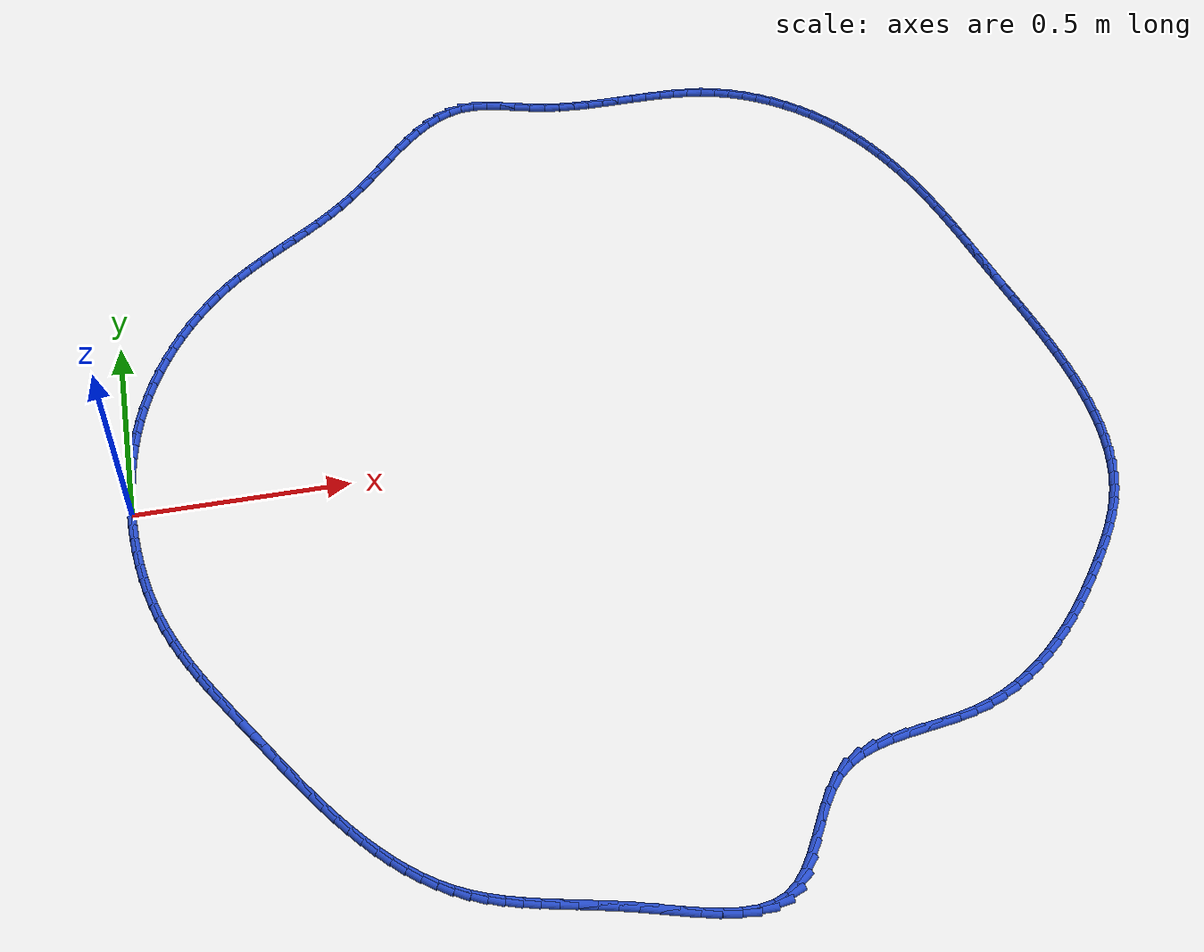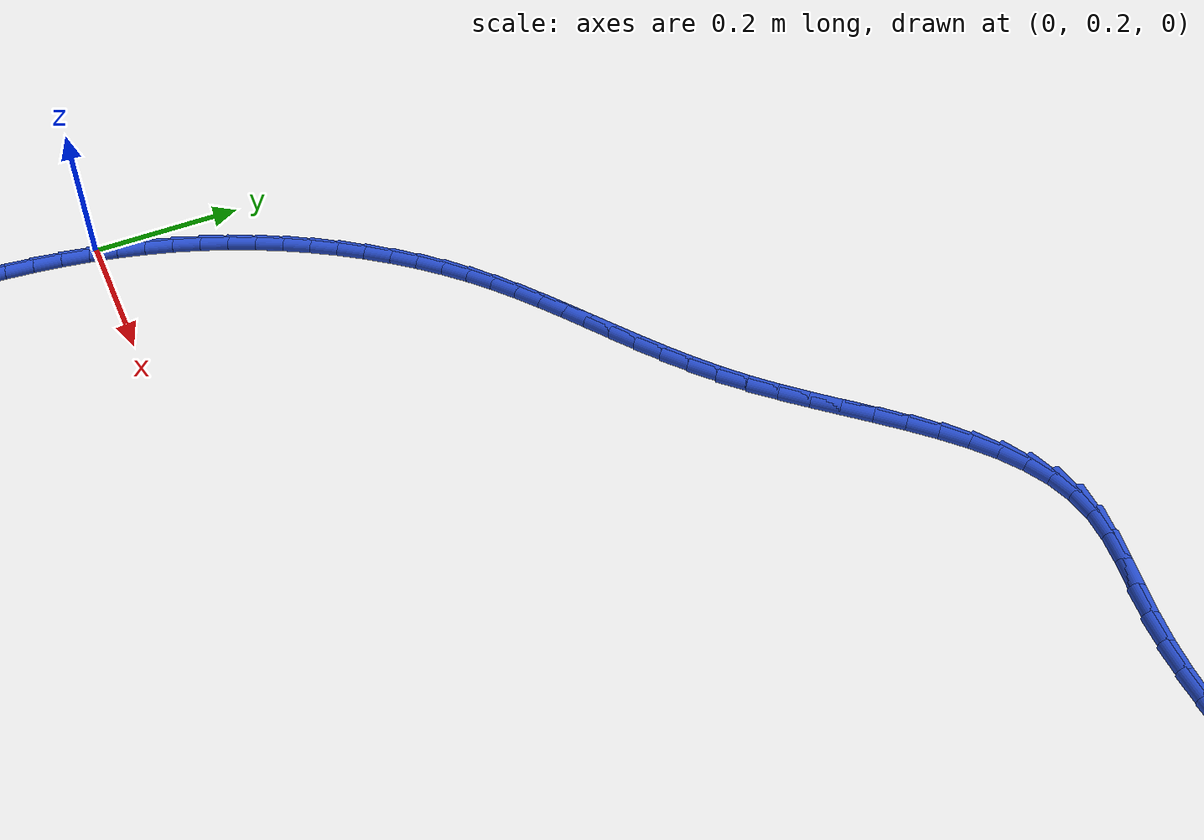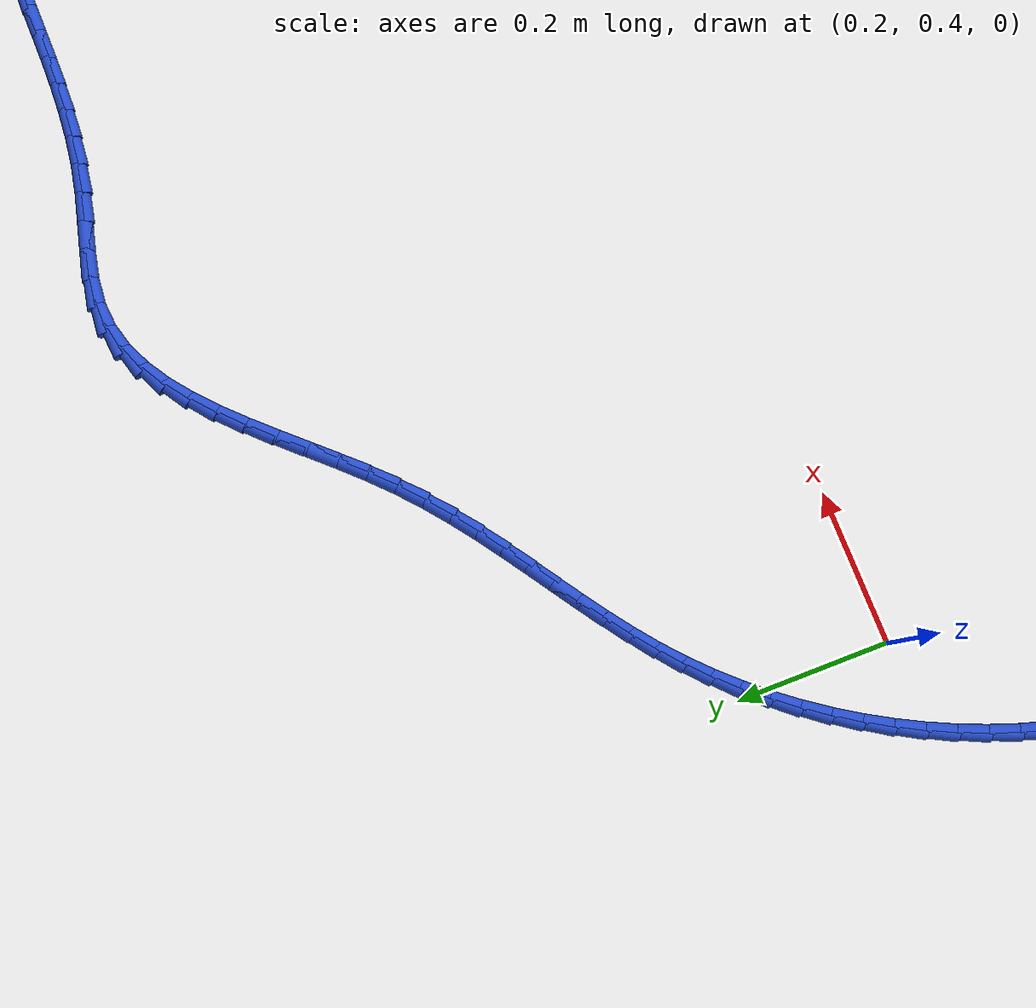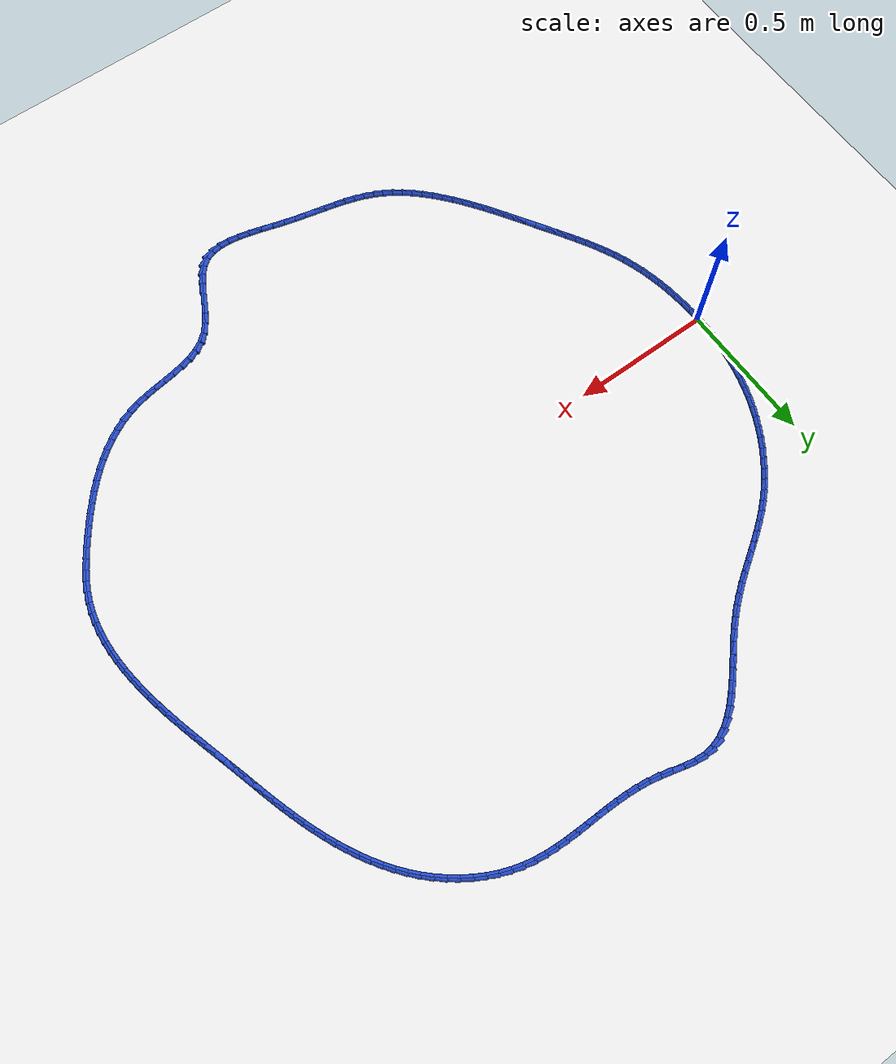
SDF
<sdf version="1.6">
 <world name="default">
  <light name="sun" type="directional">
   <pose>0 0 10 0 -0 0</pose>
   <diffuse>0.8 0.8 0.8 1</diffuse>
   <specular>0.2 0.2 0.2 1</specular>
   <attenuation>
    <range>1000</range>
    <constant>0.9</constant>
    <linear>0.01</linear>
    <quadratic>0.001</quadratic>
   </attenuation>
   <direction>-0.5 0.1 -0.9</direction>
  </light>
  <model name="ground_plane">
   <static>1</static>
   <link name="link">
    <collision name="collision">
     <geometry><plane><normal>0 0 1</normal><size>100 100</size></plane></geometry>
     <surface><friction><ode><mu>100</mu><mu2>50</mu2></ode></friction></surface>
    </collision>
    <visual name="visual">
     <cast_shadows>0</cast_shadows>
     <geometry><plane><normal>0 0 1</normal><size>100 100</size></plane></geometry>
     <material>
      <script><uri>file://media/materials/scripts/gazebo.material</uri><name>Gazebo/WhiteGlow</name></script>
     </material>
    </visual>
   </link>
  </model>
  <gravity>0 0 -9.8</gravity>
  <magnetic_field>6e-06 2.3e-05 -4.2e-05</magnetic_field>
  <atmosphere type="adiabatic"/>
  <physics name="default_physics" default="0" type="ode">
   <max_step_size>0.001</max_step_size>
   <real_time_factor>1</real_time_factor>
   <real_time_update_rate>1000</real_time_update_rate>
  </physics>
  <scene><ambient>0.4 0.4 0.4 1</ambient><background>0.7 0.7 0.7 1</background><shadows>1</shadows></scene>
  <spherical_coordinates>
   <surface_model>EARTH_WGS84</surface_model>
   <latitude_deg>0</latitude_deg>
   <longitude_deg>0</longitude_deg>
   <elevation>0</elevation>
   <heading_deg>0</heading_deg>
  </spherical_coordinates>
  <model name="line">
   <link name="link_0">
    <pose>9.540979117872439e-18 -6.938893903907228e-18 0.01 0 1.57 1.5555664343499438</pose>
    <collision name="collision">
     <geometry><cylinder><radius>0.01</radius><length>0.08</length></cylinder></geometry>
    </collision>
    <visual name="visual">
     <material>
      <script><name>Gazebo/Blue</name><uri>file://media/materials/scripts/gazebo.material</uri></script>
     </material>
     <geometry><cylinder><radius>0.01</radius><length>0.08</length></cylinder></geometry>
    </visual>
   </link>
   <link name="link_1">
    <pose>0.0005775177569326404 0.03791708356798158 0.01 0 1.57 1.5206145027544753</pose>
    <collision name="collision">
     <geometry><cylinder><radius>0.01</radius><length>0.08</length></cylinder></geometry>
    </collision>
    <visual name="visual">
     <material>
      <script><name>Gazebo/Blue</name><uri>file://media/materials/scripts/gazebo.material</uri></script>
     </material>
     <geometry><cylinder><radius>0.01</radius><length>0.08</length></cylinder></geometry>
    </visual>
   </link>
   <link name="link_2">
    <pose>0.002475163760640958 0.07570074087113149 0.01 0 1.57 1.4840044917962172</pose>
    <collision name="collision">
     <geometry><cylinder><radius>0.01</radius><length>0.08</length></cylinder></geometry>
    </collision>
    <visual name="visual">
     <material>
      <script><name>Gazebo/Blue</name><uri>file://media/materials/scripts/gazebo.material</uri></script>
     </material>
     <geometry><cylinder><radius>0.01</radius><length>0.08</length></cylinder></geometry>
    </visual>
   </link>
   <link name="link_3">
    <pose>0.005747601682768005 0.11331046412042428 0.01 0 1.57 1.4457177633226181</pose>
    <collision name="collision">
     <geometry><cylinder><radius>0.01</radius><length>0.08</length></cylinder></geometry>
    </collision>
    <visual name="visual">
     <material>
      <script><name>Gazebo/Blue</name><uri>file://media/materials/scripts/gazebo.material</uri></script>
     </material>
     <geometry><cylinder><radius>0.01</radius><length>0.08</length></cylinder></geometry>
    </visual>
   </link>
   <link name="link_4">
    <pose>0.010449495194956807 0.15070574552683452 0.01 0 1.57 1.4057535540324855</pose>
    <collision name="collision">
     <geometry><cylinder><radius>0.01</radius><length>0.08</length></cylinder></geometry>
    </collision>
    <visual name="visual">
     <material>
      <script><name>Gazebo/Blue</name><uri>file://media/materials/scripts/gazebo.material</uri></script>
     </material>
     <geometry><cylinder><radius>0.01</radius><length>0.08</length></cylinder></geometry>
    </visual>
   </link>
   <link name="link_5">
    <pose>0.016635507968850397 0.18784607730133668 0.01 0 1.57 1.3641324108347637</pose>
    <collision name="collision">
     <geometry><cylinder><radius>0.01</radius><length>0.08</length></cylinder></geometry>
    </collision>
    <visual name="visual">
     <material>
      <script><name>Gazebo/Blue</name><uri>file://media/materials/scripts/gazebo.material</uri></script>
     </material>
     <geometry><cylinder><radius>0.01</radius><length>0.08</length></cylinder></geometry>
    </visual>
   </link>
   <link name="link_6">
    <pose>0.02436030367609182 0.22469095165490532 0.01 0 1.57 1.320899511959379</pose>
    <collision name="collision">
     <geometry><cylinder><radius>0.01</radius><length>0.08</length></cylinder></geometry>
    </collision>
    <visual name="visual">
     <material>
      <script><name>Gazebo/Blue</name><uri>file://media/materials/scripts/gazebo.material</uri></script>
     </material>
     <geometry><cylinder><radius>0.01</radius><length>0.08</length></cylinder></geometry>
    </visual>
   </link>
   <link name="link_7">
    <pose>0.03367854598832409 0.26119986079851504 0.01 0 1.57 1.2761276148134053</pose>
    <collision name="collision">
     <geometry><cylinder><radius>0.01</radius><length>0.08</length></cylinder></geometry>
    </collision>
    <visual name="visual">
     <material>
      <script><name>Gazebo/Blue</name><uri>file://media/materials/scripts/gazebo.material</uri></script>
     </material>
     <geometry><cylinder><radius>0.01</radius><length>0.08</length></cylinder></geometry>
    </visual>
   </link>
   <link name="link_8">
    <pose>0.04464489857719027 0.29733229694314034 0.01 0 1.57 1.229924583732213</pose>
    <collision name="collision">
     <geometry><cylinder><radius>0.01</radius><length>0.08</length></cylinder></geometry>
    </collision>
    <visual name="visual">
     <material>
      <script><name>Gazebo/Blue</name><uri>file://media/materials/scripts/gazebo.material</uri></script>
     </material>
     <geometry><cylinder><radius>0.01</radius><length>0.08</length></cylinder></geometry>
    </visual>
   </link>
   <link name="link_9">
    <pose>0.05731375742164818 0.3330475937956359 0.01 0 1.57 1.1831204361742982</pose>
    <collision name="collision">
     <geometry><cylinder><radius>0.01</radius><length>0.08</length></cylinder></geometry>
    </collision>
    <visual name="visual">
     <material>
      <script><name>Gazebo/Blue</name><uri>file://media/materials/scripts/gazebo.material</uri></script>
     </material>
     <geometry><cylinder><radius>0.01</radius><length>0.08</length></cylinder></geometry>
    </visual>
   </link>
   <link name="link_10">
    <pose>0.0717016764282707 0.36828267830798417 0.01 0 1.57 1.1370509963883229</pose>
    <collision name="collision">
     <geometry><cylinder><radius>0.01</radius><length>0.08</length></cylinder></geometry>
    </collision>
    <visual name="visual">
     <material>
      <script><name>Gazebo/Blue</name><uri>file://media/materials/scripts/gazebo.material</uri></script>
     </material>
     <geometry><cylinder><radius>0.01</radius><length>0.08</length></cylinder></geometry>
    </visual>
   </link>
   <link name="link_11">
    <pose>0.08774858320792908 0.4029291060633097 0.01 0 1.57 1.0916071902258262</pose>
    <collision name="collision">
     <geometry><cylinder><radius>0.01</radius><length>0.08</length></cylinder></geometry>
    </collision>
    <visual name="visual">
     <material>
      <script><name>Gazebo/Blue</name><uri>file://media/materials/scripts/gazebo.material</uri></script>
     </material>
     <geometry><cylinder><radius>0.01</radius><length>0.08</length></cylinder></geometry>
    </visual>
   </link>
   <link name="link_12">
    <pose>0.10538514813811185 0.436872951323389 0.01 0 1.57 1.0465001491867596</pose>
    <collision name="collision">
     <geometry><cylinder><radius>0.01</radius><length>0.08</length></cylinder></geometry>
    </collision>
    <visual name="visual">
     <material>
      <script><name>Gazebo/Blue</name><uri>file://media/materials/scripts/gazebo.material</uri></script>
     </material>
     <geometry><cylinder><radius>0.01</radius><length>0.08</length></cylinder></geometry>
    </visual>
   </link>
   <link name="link_13">
    <pose>0.12454204159630758 0.47000028834999896 0.01 0 1.57 1.0014418363851505</pose>
    <collision name="collision">
     <geometry><cylinder><radius>0.01</radius><length>0.08</length></cylinder></geometry>
    </collision>
    <visual name="visual">
     <material>
      <script><name>Gazebo/Blue</name><uri>file://media/materials/scripts/gazebo.material</uri></script>
     </material>
     <geometry><cylinder><radius>0.01</radius><length>0.08</length></cylinder></geometry>
    </visual>
   </link>
   <link name="link_14">
    <pose>0.14514993396000475 0.5021971914049159 0.01 0 1.57 0.9561434220914788</pose>
    <collision name="collision">
     <geometry><cylinder><radius>0.01</radius><length>0.08</length></cylinder></geometry>
    </collision>
    <visual name="visual">
     <material>
      <script><name>Gazebo/Blue</name><uri>file://media/materials/scripts/gazebo.material</uri></script>
     </material>
     <geometry><cylinder><radius>0.01</radius><length>0.08</length></cylinder></geometry>
    </visual>
   </link>
   <link name="link_15">
    <pose>0.16713949560669208 0.5333497347499172 0.01 0 1.57 0.9103135712230511</pose>
    <collision name="collision">
     <geometry><cylinder><radius>0.01</radius><length>0.08</length></cylinder></geometry>
    </collision>
    <visual name="visual">
     <material>
      <script><name>Gazebo/Blue</name><uri>file://media/materials/scripts/gazebo.material</uri></script>
     </material>
     <geometry><cylinder><radius>0.01</radius><length>0.08</length></cylinder></geometry>
    </visual>
   </link>
   <link name="link_16">
    <pose>0.19044139691385803 0.5633439926467791 0.01 0 1.57 0.8636568909752695</pose>
    <collision name="collision">
     <geometry><cylinder><radius>0.01</radius><length>0.08</length></cylinder></geometry>
    </collision>
    <visual name="visual">
     <material>
      <script><name>Gazebo/Blue</name><uri>file://media/materials/scripts/gazebo.material</uri></script>
     </material>
     <geometry><cylinder><radius>0.01</radius><length>0.08</length></cylinder></geometry>
    </visual>
   </link>
   <link name="link_17">
    <pose>0.2149863082589912 0.5920660393572788 0.01 0 1.57 0.8158728126195844</pose>
    <collision name="collision">
     <geometry><cylinder><radius>0.01</radius><length>0.08</length></cylinder></geometry>
    </collision>
    <visual name="visual">
     <material>
      <script><name>Gazebo/Blue</name><uri>file://media/materials/scripts/gazebo.material</uri></script>
     </material>
     <geometry><cylinder><radius>0.01</radius><length>0.08</length></cylinder></geometry>
    </visual>
   </link>
   <link name="link_18">
    <pose>0.24070490001958017 0.6194019491431924 0.01 0 1.57 0.7666552366079411</pose>
    <collision name="collision">
     <geometry><cylinder><radius>0.01</radius><length>0.08</length></cylinder></geometry>
    </collision>
    <visual name="visual">
     <material>
      <script><name>Gazebo/Blue</name><uri>file://media/materials/scripts/gazebo.material</uri></script>
     </material>
     <geometry><cylinder><radius>0.01</radius><length>0.08</length></cylinder></geometry>
    </visual>
   </link>
   <link name="link_19">
    <pose>0.26752784257311335 0.6452377962662971 0.01 0 1.57 0.7161076845523342</pose>
    <collision name="collision">
     <geometry><cylinder><radius>0.01</radius><length>0.08</length></cylinder></geometry>
    </collision>
    <visual name="visual">
     <material>
      <script><name>Gazebo/Blue</name><uri>file://media/materials/scripts/gazebo.material</uri></script>
     </material>
     <geometry><cylinder><radius>0.01</radius><length>0.08</length></cylinder></geometry>
    </visual>
   </link>
   <link name="link_20">
    <pose>0.2953824990235863 0.669477052648196 0.01 0 1.57 0.6703020813102444</pose>
    <collision name="collision">
     <geometry><cylinder><radius>0.01</radius><length>0.08</length></cylinder></geometry>
    </collision>
    <visual name="visual">
     <material>
      <script><name>Gazebo/Blue</name><uri>file://media/materials/scripts/gazebo.material</uri></script>
     </material>
     <geometry><cylinder><radius>0.01</radius><length>0.08</length></cylinder></geometry>
    </visual>
   </link>
   <link name="link_21">
    <pose>0.32414735993053084 0.6922802805010936 0.01 0 1.57 0.6344823692075793</pose>
    <collision name="collision">
     <geometry><cylinder><radius>0.01</radius><length>0.08</length></cylinder></geometry>
    </collision>
    <visual name="visual">
     <material>
      <script><name>Gazebo/Blue</name><uri>file://media/materials/scripts/gazebo.material</uri></script>
     </material>
     <geometry><cylinder><radius>0.01</radius><length>0.08</length></cylinder></geometry>
    </visual>
   </link>
   <link name="link_22">
    <pose>0.3536636052823329 0.7140043114494673 0.01 0 1.57 0.6091887410259094</pose>
    <collision name="collision">
     <geometry><cylinder><radius>0.01</radius><length>0.08</length></cylinder></geometry>
    </collision>
    <visual name="visual">
     <material>
      <script><name>Gazebo/Blue</name><uri>file://media/materials/scripts/gazebo.material</uri></script>
     </material>
     <geometry><cylinder><radius>0.01</radius><length>0.08</length></cylinder></geometry>
    </visual>
   </link>
   <link name="link_23">
    <pose>0.3837714731374508 0.7350109320683031 0.01 0 1.57 0.5945743266580592</pose>
    <collision name="collision">
     <geometry><cylinder><radius>0.01</radius><length>0.08</length></cylinder></geometry>
    </collision>
    <visual name="visual">
     <material>
      <script><name>Gazebo/Blue</name><uri>file://media/materials/scripts/gazebo.material</uri></script>
     </material>
     <geometry><cylinder><radius>0.01</radius><length>0.08</length></cylinder></geometry>
    </visual>
   </link>
   <link name="link_24">
    <pose>0.4143112015543421 0.7556619289325864 0.01 0 1.57 0.5906031621618749</pose>
    <collision name="collision">
     <geometry><cylinder><radius>0.01</radius><length>0.08</length></cylinder></geometry>
    </collision>
    <visual name="visual">
     <material>
      <script><name>Gazebo/Blue</name><uri>file://media/materials/scripts/gazebo.material</uri></script>
     </material>
     <geometry><cylinder><radius>0.01</radius><length>0.08</length></cylinder></geometry>
    </visual>
   </link>
   <link name="link_25">
    <pose>0.4451230285914648 0.7763190886173033 0.01 0 1.57 0.5971031915808017</pose>
    <collision name="collision">
     <geometry><cylinder><radius>0.01</radius><length>0.08</length></cylinder></geometry>
    </collision>
    <visual name="visual">
     <material>
      <script><name>Gazebo/Blue</name><uri>file://media/materials/scripts/gazebo.material</uri></script>
     </material>
     <geometry><cylinder><radius>0.01</radius><length>0.08</length></cylinder></geometry>
    </visual>
   </link>
   <link name="link_26">
    <pose>0.47604719230727727 0.7973441976974392 0.01 0 1.57 0.6137869619989732</pose>
    <collision name="collision">
     <geometry><cylinder><radius>0.01</radius><length>0.08</length></cylinder></geometry>
    </collision>
    <visual name="visual">
     <material>
      <script><name>Gazebo/Blue</name><uri>file://media/materials/scripts/gazebo.material</uri></script>
     </material>
     <geometry><cylinder><radius>0.01</radius><length>0.08</length></cylinder></geometry>
    </visual>
   </link>
   <link name="link_27">
    <pose>0.5069239307602369 0.8190990427479798 0.01 0 1.57 0.640242088138318</pose>
    <collision name="collision">
     <geometry><cylinder><radius>0.01</radius><length>0.08</length></cylinder></geometry>
    </collision>
    <visual name="visual">
     <material>
      <script><name>Gazebo/Blue</name><uri>file://media/materials/scripts/gazebo.material</uri></script>
     </material>
     <geometry><cylinder><radius>0.01</radius><length>0.08</length></cylinder></geometry>
    </visual>
   </link>
   <link name="link_28">
    <pose>0.5375934820088019 0.8419454103439106 0.01 0 1.57 0.6758988090316247</pose>
    <collision name="collision">
     <geometry><cylinder><radius>0.01</radius><length>0.08</length></cylinder></geometry>
    </collision>
    <visual name="visual">
     <material>
      <script><name>Gazebo/Blue</name><uri>file://media/materials/scripts/gazebo.material</uri></script>
     </material>
     <geometry><cylinder><radius>0.01</radius><length>0.08</length></cylinder></geometry>
    </visual>
   </link>
   <link name="link_29">
    <pose>0.5678960841114301 0.8662450870602177 0.01 0 1.57 0.7199866024371995</pose>
    <collision name="collision">
     <geometry><cylinder><radius>0.01</radius><length>0.08</length></cylinder></geometry>
    </collision>
    <visual name="visual">
     <material>
      <script><name>Gazebo/Blue</name><uri>file://media/materials/scripts/gazebo.material</uri></script>
     </material>
     <geometry><cylinder><radius>0.01</radius><length>0.08</length></cylinder></geometry>
    </visual>
   </link>
   <link name="link_30">
    <pose>0.5976719751265794 0.8923598594718863 0.01 0 1.57 0.7692092500154342</pose>
    <collision name="collision">
     <geometry><cylinder><radius>0.01</radius><length>0.08</length></cylinder></geometry>
    </collision>
    <visual name="visual">
     <material>
      <script><name>Gazebo/Blue</name><uri>file://media/materials/scripts/gazebo.material</uri></script>
     </material>
     <geometry><cylinder><radius>0.01</radius><length>0.08</length></cylinder></geometry>
    </visual>
   </link>
   <link name="link_31">
    <pose>0.6267924940909677 0.9205524602406285 0.01 0 1.57 0.8067644135835703</pose>
    <collision name="collision">
     <geometry><cylinder><radius>0.01</radius><length>0.08</length></cylinder></geometry>
    </collision>
    <visual name="visual">
     <material>
      <script><name>Gazebo/Blue</name><uri>file://media/materials/scripts/gazebo.material</uri></script>
     </material>
     <geometry><cylinder><radius>0.01</radius><length>0.08</length></cylinder></geometry>
    </visual>
   </link>
   <link name="link_32">
    <pose>0.6553558070791505 0.9503631976225067 0.01 0 1.57 0.8269070133763471</pose>
    <collision name="collision">
     <geometry><cylinder><radius>0.01</radius><length>0.08</length></cylinder></geometry>
    </collision>
    <visual name="visual">
     <material>
      <script><name>Gazebo/Blue</name><uri>file://media/materials/scripts/gazebo.material</uri></script>
     </material>
     <geometry><cylinder><radius>0.01</radius><length>0.08</length></cylinder></geometry>
    </visual>
   </link>
   <link name="link_33">
    <pose>0.6835605715791226 0.9810123234538641 0.01 0 1.57 0.8306597712886247</pose>
    <collision name="collision">
     <geometry><cylinder><radius>0.01</radius><length>0.08</length></cylinder></geometry>
    </collision>
    <visual name="visual">
     <material>
      <script><name>Gazebo/Blue</name><uri>file://media/materials/scripts/gazebo.material</uri></script>
     </material>
     <geometry><cylinder><radius>0.01</radius><length>0.08</length></cylinder></geometry>
    </visual>
   </link>
   <link name="link_34">
    <pose>0.7116058944903185 1.0117186582346613 0.01 0 1.57 0.8180619769598371</pose>
    <collision name="collision">
     <geometry><cylinder><radius>0.01</radius><length>0.08</length></cylinder></geometry>
    </collision>
    <visual name="visual">
     <material>
      <script><name>Gazebo/Blue</name><uri>file://media/materials/scripts/gazebo.material</uri></script>
     </material>
     <geometry><cylinder><radius>0.01</radius><length>0.08</length></cylinder></geometry>
    </visual>
   </link>
   <link name="link_35">
    <pose>0.7396908827121714 1.0417010224648573 0.01 0 1.57 0.7880997609549949</pose>
    <collision name="collision">
     <geometry><cylinder><radius>0.01</radius><length>0.08</length></cylinder></geometry>
    </collision>
    <visual name="visual">
     <material>
      <script><name>Gazebo/Blue</name><uri>file://media/materials/scripts/gazebo.material</uri></script>
     </material>
     <geometry><cylinder><radius>0.01</radius><length>0.08</length></cylinder></geometry>
    </visual>
   </link>
   <link name="link_36">
    <pose>0.768014643144116 1.0701782366444128 0.01 0 1.57 0.7386508656800419</pose>
    <collision name="collision">
     <geometry><cylinder><radius>0.01</radius><length>0.08</length></cylinder></geometry>
    </collision>
    <visual name="visual">
     <material>
      <script><name>Gazebo/Blue</name><uri>file://media/materials/scripts/gazebo.material</uri></script>
     </material>
     <geometry><cylinder><radius>0.01</radius><length>0.08</length></cylinder></geometry>
    </visual>
   </link>
   <link name="link_37">
    <pose>0.796776282685586 1.0963691212732876 0.01 0 1.57 0.6664833649199631</pose>
    <collision name="collision">
     <geometry><cylinder><radius>0.01</radius><length>0.08</length></cylinder></geometry>
    </collision>
    <visual name="visual">
     <material>
      <script><name>Gazebo/Blue</name><uri>file://media/materials/scripts/gazebo.material</uri></script>
     </material>
     <geometry><cylinder><radius>0.01</radius><length>0.08</length></cylinder></geometry>
    </visual>
   </link>
   <link name="link_38">
    <pose>0.8261749082360152 1.1194924968514415 0.01 0 1.57 0.5675388949383757</pose>
    <collision name="collision">
     <geometry><cylinder><radius>0.01</radius><length>0.08</length></cylinder></geometry>
    </collision>
    <visual name="visual">
     <material>
      <script><name>Gazebo/Blue</name><uri>file://media/materials/scripts/gazebo.material</uri></script>
     </material>
     <geometry><cylinder><radius>0.01</radius><length>0.08</length></cylinder></geometry>
    </visual>
   </link>
   <link name="link_39">
    <pose>0.8564096266948384 1.1387671838788347 0.01 0 1.57 0.4379968372913615</pose>
    <collision name="collision">
     <geometry><cylinder><radius>0.01</radius><length>0.08</length></cylinder></geometry>
    </collision>
    <visual name="visual">
     <material>
      <script><name>Gazebo/Blue</name><uri>file://media/materials/scripts/gazebo.material</uri></script>
     </material>
     <geometry><cylinder><radius>0.01</radius><length>0.08</length></cylinder></geometry>
    </visual>
   </link>
   <link name="link_40">
    <pose>0.8876795449614888 1.1534120028554269 0.01 0 1.57 0.2767872441954829</pose>
    <collision name="collision">
     <geometry><cylinder><radius>0.01</radius><length>0.08</length></cylinder></geometry>
    </collision>
    <visual name="visual">
     <material>
      <script><name>Gazebo/Blue</name><uri>file://media/materials/scripts/gazebo.material</uri></script>
     </material>
     <geometry><cylinder><radius>0.01</radius><length>0.08</length></cylinder></geometry>
    </visual>
   </link>
   <link name="link_41">
    <pose>0.9201837699354012 1.1626457742811784 0.01 0 1.57 0.08949335892013556</pose>
    <collision name="collision">
     <geometry><cylinder><radius>0.01</radius><length>0.08</length></cylinder></geometry>
    </collision>
    <visual name="visual">
     <material>
      <script><name>Gazebo/Blue</name><uri>file://media/materials/scripts/gazebo.material</uri></script>
     </material>
     <geometry><cylinder><radius>0.01</radius><length>0.08</length></cylinder></geometry>
    </visual>
   </link>
   <link name="link_42">
    <pose>0.9541207168398046 1.1656910399016565 0.01 0 1.57 -0.08751346400719535</pose>
    <collision name="collision">
     <geometry><cylinder><radius>0.01</radius><length>0.08</length></cylinder></geometry>
    </collision>
    <visual name="visual">
     <material>
      <script><name>Gazebo/Blue</name><uri>file://media/materials/scripts/gazebo.material</uri></script>
     </material>
     <geometry><cylinder><radius>0.01</radius><length>0.08</length></cylinder></geometry>
    </visual>
   </link>
   <link name="link_43">
    <pose>0.989537630114699 1.1625836463151902 0.01 0 1.57 -0.19940601137576291</pose>
    <collision name="collision">
     <geometry><cylinder><radius>0.01</radius><length>0.08</length></cylinder></geometry>
    </collision>
    <visual name="visual">
     <material>
      <script><name>Gazebo/Blue</name><uri>file://media/materials/scripts/gazebo.material</uri></script>
     </material>
     <geometry><cylinder><radius>0.01</radius><length>0.08</length></cylinder></geometry>
    </visual>
   </link>
   <link name="link_44">
    <pose>1.0261422172297148 1.1551861625845183 0.01 0 1.57 -0.2503121058701938</pose>
    <collision name="collision">
     <geometry><cylinder><radius>0.01</radius><length>0.08</length></cylinder></geometry>
    </collision>
    <visual name="visual">
     <material>
      <script><name>Gazebo/Blue</name><uri>file://media/materials/scripts/gazebo.material</uri></script>
     </material>
     <geometry><cylinder><radius>0.01</radius><length>0.08</length></cylinder></geometry>
    </visual>
   </link>
   <link name="link_45">
    <pose>1.0635958925514435 1.1456102165160535 0.01 0 1.57 -0.24873682755634025</pose>
    <collision name="collision">
     <geometry><cylinder><radius>0.01</radius><length>0.08</length></cylinder></geometry>
    </collision>
    <visual name="visual">
     <material>
      <script><name>Gazebo/Blue</name><uri>file://media/materials/scripts/gazebo.material</uri></script>
     </material>
     <geometry><cylinder><radius>0.01</radius><length>0.08</length></cylinder></geometry>
    </visual>
   </link>
   <link name="link_46">
    <pose>1.101560070446477 1.1359674359162086 0.01 0 1.57 -0.1992889178391938</pose>
    <collision name="collision">
     <geometry><cylinder><radius>0.01</radius><length>0.08</length></cylinder></geometry>
    </collision>
    <visual name="visual">
     <material>
      <script><name>Gazebo/Blue</name><uri>file://media/materials/scripts/gazebo.material</uri></script>
     </material>
     <geometry><cylinder><radius>0.01</radius><length>0.08</length></cylinder></geometry>
    </visual>
   </link>
   <link name="link_47">
    <pose>1.1397087469627167 1.1282625538016797 0.01 0 1.57 -0.1350952710099654</pose>
    <collision name="collision">
     <geometry><cylinder><radius>0.01</radius><length>0.08</length></cylinder></geometry>
    </collision>
    <visual name="visual">
     <material>
      <script><name>Gazebo/Blue</name><uri>file://media/materials/scripts/gazebo.material</uri></script>
     </material>
     <geometry><cylinder><radius>0.01</radius><length>0.08</length></cylinder></geometry>
    </visual>
   </link>
   <link name="link_48">
    <pose>1.1778838345319351 1.1230736745773449 0.01 0 1.57 -0.08133392156681518</pose>
    <collision name="collision">
     <geometry><cylinder><radius>0.01</radius><length>0.08</length></cylinder></geometry>
    </collision>
    <visual name="visual">
     <material>
      <script><name>Gazebo/Blue</name><uri>file://media/materials/scripts/gazebo.material</uri></script>
     </material>
     <geometry><cylinder><radius>0.01</radius><length>0.08</length></cylinder></geometry>
    </visual>
   </link>
   <link name="link_49">
    <pose>1.2160468347179172 1.1199628655380338 0.01 0 1.57 -0.03913708060453807</pose>
    <collision name="collision">
     <geometry><cylinder><radius>0.01</radius><length>0.08</length></cylinder></geometry>
    </collision>
    <visual name="visual">
     <material>
      <script><name>Gazebo/Blue</name><uri>file://media/materials/scripts/gazebo.material</uri></script>
     </material>
     <geometry><cylinder><radius>0.01</radius><length>0.08</length></cylinder></geometry>
    </visual>
   </link>
   <link name="link_50">
    <pose>1.2541618149288882 1.1184703943959258 0.01 0 1.57 -0.00877854155304162</pose>
    <collision name="collision">
     <geometry><cylinder><radius>0.01</radius><length>0.08</length></cylinder></geometry>
    </collision>
    <visual name="visual">
     <material>
      <script><name>Gazebo/Blue</name><uri>file://media/materials/scripts/gazebo.material</uri></script>
     </material>
     <geometry><cylinder><radius>0.01</radius><length>0.08</length></cylinder></geometry>
    </visual>
   </link>
   <link name="link_51">
    <pose>1.292192842573071 1.118136528863199 0.01 0 1.57 0.009627684290932397</pose>
    <collision name="collision">
     <geometry><cylinder><radius>0.01</radius><length>0.08</length></cylinder></geometry>
    </collision>
    <visual name="visual">
     <material>
      <script><name>Gazebo/Blue</name><uri>file://media/materials/scripts/gazebo.material</uri></script>
     </material>
     <geometry><cylinder><radius>0.01</radius><length>0.08</length></cylinder></geometry>
    </visual>
   </link>
   <link name="link_52">
    <pose>1.3301039850586902 1.1185015366520332 0.01 0 1.57 0.016000319685674228</pose>
    <collision name="collision">
     <geometry><cylinder><radius>0.01</radius><length>0.08</length></cylinder></geometry>
    </collision>
    <visual name="visual">
     <material>
      <script><name>Gazebo/Blue</name><uri>file://media/materials/scripts/gazebo.material</uri></script>
     </material>
     <geometry><cylinder><radius>0.01</radius><length>0.08</length></cylinder></geometry>
    </visual>
   </link>
   <link name="link_53">
    <pose>1.367859309793969 1.119105685474607 0.01 0 1.57 0.01021053627949765</pose>
    <collision name="collision">
     <geometry><cylinder><radius>0.01</radius><length>0.08</length></cylinder></geometry>
    </collision>
    <visual name="visual">
     <material>
      <script><name>Gazebo/Blue</name><uri>file://media/materials/scripts/gazebo.material</uri></script>
     </material>
     <geometry><cylinder><radius>0.01</radius><length>0.08</length></cylinder></geometry>
    </visual>
   </link>
   <link name="link_54">
    <pose>1.4054228841871328 1.1194892430431 0.01 0 1.57 -0.007948376541187201</pose>
    <collision name="collision">
     <geometry><cylinder><radius>0.01</radius><length>0.08</length></cylinder></geometry>
    </collision>
    <visual name="visual">
     <material>
      <script><name>Gazebo/Blue</name><uri>file://media/materials/scripts/gazebo.material</uri></script>
     </material>
     <geometry><cylinder><radius>0.01</radius><length>0.08</length></cylinder></geometry>
    </visual>
   </link>
   <link name="link_55">
    <pose>1.4427587756464044 1.1191924770696906 0.01 0 1.57 -0.038737924337312116</pose>
    <collision name="collision">
     <geometry><cylinder><radius>0.01</radius><length>0.08</length></cylinder></geometry>
    </collision>
    <visual name="visual">
     <material>
      <script><name>Gazebo/Blue</name><uri>file://media/materials/scripts/gazebo.material</uri></script>
     </material>
     <geometry><cylinder><radius>0.01</radius><length>0.08</length></cylinder></geometry>
    </visual>
   </link>
   <link name="link_56">
    <pose>1.479831051580008 1.1177556552665584 0.01 0 1.57 -0.08239083419778048</pose>
    <collision name="collision">
     <geometry><cylinder><radius>0.01</radius><length>0.08</length></cylinder></geometry>
    </collision>
    <visual name="visual">
     <material>
      <script><name>Gazebo/Blue</name><uri>file://media/materials/scripts/gazebo.material</uri></script>
     </material>
     <geometry><cylinder><radius>0.01</radius><length>0.08</length></cylinder></geometry>
    </visual>
   </link>
   <link name="link_57">
    <pose>1.5166037793961682 1.114719045345882 0.01 0 1.57 -0.1389590862366496</pose>
    <collision name="collision">
     <geometry><cylinder><radius>0.01</radius><length>0.08</length></cylinder></geometry>
    </collision>
    <visual name="visual">
     <material>
      <script><name>Gazebo/Blue</name><uri>file://media/materials/scripts/gazebo.material</uri></script>
     </material>
     <geometry><cylinder><radius>0.01</radius><length>0.08</length></cylinder></geometry>
    </visual>
   </link>
   <link name="link_58">
    <pose>1.5530410265031085 1.1096229150198407 0.01 0 1.57 -0.20809554832139596</pose>
    <collision name="collision">
     <geometry><cylinder><radius>0.01</radius><length>0.08</length></cylinder></geometry>
    </collision>
    <visual name="visual">
     <material>
      <script><name>Gazebo/Blue</name><uri>file://media/materials/scripts/gazebo.material</uri></script>
     </material>
     <geometry><cylinder><radius>0.01</radius><length>0.08</length></cylinder></geometry>
    </visual>
   </link>
   <link name="link_59">
    <pose>1.5891068603090526 1.102007532000613 0.01 0 1.57 -0.2867719032216477</pose>
    <collision name="collision">
     <geometry><cylinder><radius>0.01</radius><length>0.08</length></cylinder></geometry>
    </collision>
    <visual name="visual">
     <material>
      <script><name>Gazebo/Blue</name><uri>file://media/materials/scripts/gazebo.material</uri></script>
     </material>
     <geometry><cylinder><radius>0.01</radius><length>0.08</length></cylinder></geometry>
    </visual>
   </link>
   <link name="link_60">
    <pose>1.6247459759272804 1.091497535483131 0.01 0 1.57 -0.36375254858053074</pose>
    <collision name="collision">
     <geometry><cylinder><radius>0.01</radius><length>0.08</length></cylinder></geometry>
    </collision>
    <visual name="visual">
     <material>
      <script><name>Gazebo/Blue</name><uri>file://media/materials/scripts/gazebo.material</uri></script>
     </material>
     <geometry><cylinder><radius>0.01</radius><length>0.08</length></cylinder></geometry>
    </visual>
   </link>
   <link name="link_61">
    <pose>1.6598034585186796 1.0781513924253054 0.01 0 1.57 -0.4362256728753696</pose>
    <collision name="collision">
     <geometry><cylinder><radius>0.01</radius><length>0.08</length></cylinder></geometry>
    </collision>
    <visual name="visual">
     <material>
      <script><name>Gazebo/Blue</name><uri>file://media/materials/scripts/gazebo.material</uri></script>
     </material>
     <geometry><cylinder><radius>0.01</radius><length>0.08</length></cylinder></geometry>
    </visual>
   </link>
   <link name="link_62">
    <pose>1.6940924671043063 1.0621666165920467 0.01 0 1.57 -0.5049667959516304</pose>
    <collision name="collision">
     <geometry><cylinder><radius>0.01</radius><length>0.08</length></cylinder></geometry>
    </collision>
    <visual name="visual">
     <material>
      <script><name>Gazebo/Blue</name><uri>file://media/materials/scripts/gazebo.material</uri></script>
     </material>
     <geometry><cylinder><radius>0.01</radius><length>0.08</length></cylinder></geometry>
    </visual>
   </link>
   <link name="link_63">
    <pose>1.7274261461274572 1.043740785238263 0.01 0 1.57 -0.5707828892560924</pose>
    <collision name="collision">
     <geometry><cylinder><radius>0.01</radius><length>0.08</length></cylinder></geometry>
    </collision>
    <visual name="visual">
     <material>
      <script><name>Gazebo/Blue</name><uri>file://media/materials/scripts/gazebo.material</uri></script>
     </material>
     <geometry><cylinder><radius>0.01</radius><length>0.08</length></cylinder></geometry>
    </visual>
   </link>
   <link name="link_64">
    <pose>1.7596176400314312 1.0230714756188637 0.01 0 1.57 -0.6344900885407306</pose>
    <collision name="collision">
     <geometry><cylinder><radius>0.01</radius><length>0.08</length></cylinder></geometry>
    </collision>
    <visual name="visual">
     <material>
      <script><name>Gazebo/Blue</name><uri>file://media/materials/scripts/gazebo.material</uri></script>
     </material>
     <geometry><cylinder><radius>0.01</radius><length>0.08</length></cylinder></geometry>
    </visual>
   </link>
   <link name="link_65">
    <pose>1.7904800932595248 1.0003562649887585 0.01 0 1.57 -0.6969076532412875</pose>
    <collision name="collision">
     <geometry><cylinder><radius>0.01</radius><length>0.08</length></cylinder></geometry>
    </collision>
    <visual name="visual">
     <material>
      <script><name>Gazebo/Blue</name><uri>file://media/materials/scripts/gazebo.material</uri></script>
     </material>
     <geometry><cylinder><radius>0.01</radius><length>0.08</length></cylinder></geometry>
    </visual>
   </link>
   <link name="link_66">
    <pose>1.819826650255036 0.9757927306028568 0.01 0 1.57 -0.758807320168364</pose>
    <collision name="collision">
     <geometry><cylinder><radius>0.01</radius><length>0.08</length></cylinder></geometry>
    </collision>
    <visual name="visual">
     <material>
      <script><name>Gazebo/Blue</name><uri>file://media/materials/scripts/gazebo.material</uri></script>
     </material>
     <geometry><cylinder><radius>0.01</radius><length>0.08</length></cylinder></geometry>
    </visual>
   </link>
   <link name="link_67">
    <pose>1.8474746657595695 0.9495773265140206 0.01 0 1.57 -0.819230387233219</pose>
    <collision name="collision">
     <geometry><cylinder><radius>0.01</radius><length>0.08</length></cylinder></geometry>
    </collision>
    <visual name="visual">
     <material>
      <script><name>Gazebo/Blue</name><uri>file://media/materials/scripts/gazebo.material</uri></script>
     </material>
     <geometry><cylinder><radius>0.01</radius><length>0.08</length></cylinder></geometry>
    </visual>
   </link>
   <link name="link_68">
    <pose>1.8733643994042504 0.9218737188315165 0.01 0 1.57 -0.8762609594338301</pose>
    <collision name="collision">
     <geometry><cylinder><radius>0.01</radius><length>0.08</length></cylinder></geometry>
    </collision>
    <visual name="visual">
     <material>
      <script><name>Gazebo/Blue</name><uri>file://media/materials/scripts/gazebo.material</uri></script>
     </material>
     <geometry><cylinder><radius>0.01</radius><length>0.08</length></cylinder></geometry>
    </visual>
   </link>
   <link name="link_69">
    <pose>1.8975755216495918 0.8928083823500186 0.01 0 1.57 -0.9295640055066728</pose>
    <collision name="collision">
     <geometry><cylinder><radius>0.01</radius><length>0.08</length></cylinder></geometry>
    </collision>
    <visual name="visual">
     <material>
      <script><name>Gazebo/Blue</name><uri>file://media/materials/scripts/gazebo.material</uri></script>
     </material>
     <geometry><cylinder><radius>0.01</radius><length>0.08</length></cylinder></geometry>
    </visual>
   </link>
   <link name="link_70">
    <pose>1.9201952308841532 0.8625057836017064 0.01 0 1.57 -0.9790151249170048</pose>
    <collision name="collision">
     <geometry><cylinder><radius>0.01</radius><length>0.08</length></cylinder></geometry>
    </collision>
    <visual name="visual">
     <material>
      <script><name>Gazebo/Blue</name><uri>file://media/materials/scripts/gazebo.material</uri></script>
     </material>
     <geometry><cylinder><radius>0.01</radius><length>0.08</length></cylinder></geometry>
    </visual>
   </link>
   <link name="link_71">
    <pose>1.941310725496494 0.8310903891187572 0.01 0 1.57 -1.0245825023831916</pose>
    <collision name="collision">
     <geometry><cylinder><radius>0.01</radius><length>0.08</length></cylinder></geometry>
    </collision>
    <visual name="visual">
     <material>
      <script><name>Gazebo/Blue</name><uri>file://media/materials/scripts/gazebo.material</uri></script>
     </material>
     <geometry><cylinder><radius>0.01</radius><length>0.08</length></cylinder></geometry>
    </visual>
   </link>
   <link name="link_72">
    <pose>1.9610092038751747 0.7986866654333512 0.01 0 1.57 -1.0663048014358874</pose>
    <collision name="collision">
     <geometry><cylinder><radius>0.01</radius><length>0.08</length></cylinder></geometry>
    </collision>
    <visual name="visual">
     <material>
      <script><name>Gazebo/Blue</name><uri>file://media/materials/scripts/gazebo.material</uri></script>
     </material>
     <geometry><cylinder><radius>0.01</radius><length>0.08</length></cylinder></geometry>
    </visual>
   </link>
   <link name="link_73">
    <pose>1.9793778644087547 0.7654190790776668 0.01 0 1.57 -1.1042699420628443</pose>
    <collision name="collision">
     <geometry><cylinder><radius>0.01</radius><length>0.08</length></cylinder></geometry>
    </collision>
    <visual name="visual">
     <material>
      <script><name>Gazebo/Blue</name><uri>file://media/materials/scripts/gazebo.material</uri></script>
     </material>
     <geometry><cylinder><radius>0.01</radius><length>0.08</length></cylinder></geometry>
    </visual>
   </link>
   <link name="link_74">
    <pose>1.9965039054857934 0.7314120965838824 0.01 0 1.57 -1.138596301172894</pose>
    <collision name="collision">
     <geometry><cylinder><radius>0.01</radius><length>0.08</length></cylinder></geometry>
    </collision>
    <visual name="visual">
     <material>
      <script><name>Gazebo/Blue</name><uri>file://media/materials/scripts/gazebo.material</uri></script>
     </material>
     <geometry><cylinder><radius>0.01</radius><length>0.08</length></cylinder></geometry>
    </visual>
   </link>
   <link name="link_75">
    <pose>2.0124745254948513 0.6967901844841767 0.01 0 1.57 -1.1694169733152449</pose>
    <collision name="collision">
     <geometry><cylinder><radius>0.01</radius><length>0.08</length></cylinder></geometry>
    </collision>
    <visual name="visual">
     <material>
      <script><name>Gazebo/Blue</name><uri>file://media/materials/scripts/gazebo.material</uri></script>
     </material>
     <geometry><cylinder><radius>0.01</radius><length>0.08</length></cylinder></geometry>
    </visual>
   </link>
   <link name="link_76">
    <pose>2.027376922824487 0.6616778093107293 0.01 0 1.57 -1.1968670996404054</pose>
    <collision name="collision">
     <geometry><cylinder><radius>0.01</radius><length>0.08</length></cylinder></geometry>
    </collision>
    <visual name="visual">
     <material>
      <script><name>Gazebo/Blue</name><uri>file://media/materials/scripts/gazebo.material</uri></script>
     </material>
     <geometry><cylinder><radius>0.01</radius><length>0.08</length></cylinder></geometry>
    </visual>
   </link>
   <link name="link_77">
    <pose>2.0412982958632613 0.6261994375957177 0.01 0 1.57 -1.2210738989811984</pose>
    <collision name="collision">
     <geometry><cylinder><radius>0.01</radius><length>0.08</length></cylinder></geometry>
    </collision>
    <visual name="visual">
     <material>
      <script><name>Gazebo/Blue</name><uri>file://media/materials/scripts/gazebo.material</uri></script>
     </material>
     <geometry><cylinder><radius>0.01</radius><length>0.08</length></cylinder></geometry>
    </visual>
   </link>
   <link name="link_78">
    <pose>2.0543258429997335 0.5904795358713215 0.01 0 1.57 -1.242148853886375</pose>
    <collision name="collision">
     <geometry><cylinder><radius>0.01</radius><length>0.08</length></cylinder></geometry>
    </collision>
    <visual name="visual">
     <material>
      <script><name>Gazebo/Blue</name><uri>file://media/materials/scripts/gazebo.material</uri></script>
     </material>
     <geometry><cylinder><radius>0.01</radius><length>0.08</length></cylinder></geometry>
    </visual>
   </link>
   <link name="link_79">
    <pose>2.0665467626224636 0.5546425706697191 0.01 0 1.57 -1.260176175621361</pose>
    <collision name="collision">
     <geometry><cylinder><radius>0.01</radius><length>0.08</length></cylinder></geometry>
    </collision>
    <visual name="visual">
     <material>
      <script><name>Gazebo/Blue</name><uri>file://media/materials/scripts/gazebo.material</uri></script>
     </material>
     <geometry><cylinder><radius>0.01</radius><length>0.08</length></cylinder></geometry>
    </visual>
   </link>
   <link name="link_80">
    <pose>2.0780486508105103 0.5188124186376855 0.01 0 1.57 -1.274444658479171</pose>
    <collision name="collision">
     <geometry><cylinder><radius>0.01</radius><length>0.08</length></cylinder></geometry>
    </collision>
    <visual name="visual">
     <material>
      <script><name>Gazebo/Blue</name><uri>file://media/materials/scripts/gazebo.material</uri></script>
     </material>
     <geometry><cylinder><radius>0.01</radius><length>0.08</length></cylinder></geometry>
    </visual>
   </link>
   <link name="link_81">
    <pose>2.0889741928671937 0.4830312438104072 0.01 0 1.57 -1.2832729525572875</pose>
    <collision name="collision">
     <geometry><cylinder><radius>0.01</radius><length>0.08</length></cylinder></geometry>
    </collision>
    <visual name="visual">
     <material>
      <script><name>Gazebo/Blue</name><uri>file://media/materials/scripts/gazebo.material</uri></script>
     </material>
     <geometry><cylinder><radius>0.01</radius><length>0.08</length></cylinder></geometry>
    </visual>
   </link>
   <link name="link_82">
    <pose>2.0995770349685285 0.4471766244476499 0.01 0 1.57 -1.2863221765230024</pose>
    <collision name="collision">
     <geometry><cylinder><radius>0.01</radius><length>0.08</length></cylinder></geometry>
    </collision>
    <visual name="visual">
     <material>
      <script><name>Gazebo/Blue</name><uri>file://media/materials/scripts/gazebo.material</uri></script>
     </material>
     <geometry><cylinder><radius>0.01</radius><length>0.08</length></cylinder></geometry>
    </visual>
   </link>
   <link name="link_83">
    <pose>2.1101241440133265 0.411106380479623 0.01 0 1.57 -1.2836412811550717</pose>
    <collision name="collision">
     <geometry><cylinder><radius>0.01</radius><length>0.08</length></cylinder></geometry>
    </collision>
    <visual name="visual">
     <material>
      <script><name>Gazebo/Blue</name><uri>file://media/materials/scripts/gazebo.material</uri></script>
     </material>
     <geometry><cylinder><radius>0.01</radius><length>0.08</length></cylinder></geometry>
    </visual>
   </link>
   <link name="link_84">
    <pose>2.120881886779338 0.37467861363230387 0.01 0 1.57 -1.2780586465992638</pose>
    <collision name="collision">
     <geometry><cylinder><radius>0.01</radius><length>0.08</length></cylinder></geometry>
    </collision>
    <visual name="visual">
     <material>
      <script><name>Gazebo/Blue</name><uri>file://media/materials/scripts/gazebo.material</uri></script>
     </material>
     <geometry><cylinder><radius>0.01</radius><length>0.08</length></cylinder></geometry>
    </visual>
   </link>
   <link name="link_85">
    <pose>2.131994307797066 0.3378088638614558 0.01 0 1.57 -1.2754092566540112</pose>
    <collision name="collision">
     <geometry><cylinder><radius>0.01</radius><length>0.08</length></cylinder></geometry>
    </collision>
    <visual name="visual">
     <material>
      <script><name>Gazebo/Blue</name><uri>file://media/materials/scripts/gazebo.material</uri></script>
     </material>
     <geometry><cylinder><radius>0.01</radius><length>0.08</length></cylinder></geometry>
    </visual>
   </link>
   <link name="link_86">
    <pose>2.1433349041097305 0.3005397107177847 0.01 0 1.57 -1.2763335382882288</pose>
    <collision name="collision">
     <geometry><cylinder><radius>0.01</radius><length>0.08</length></cylinder></geometry>
    </collision>
    <visual name="visual">
     <material>
      <script><name>Gazebo/Blue</name><uri>file://media/materials/scripts/gazebo.material</uri></script>
     </material>
     <geometry><cylinder><radius>0.01</radius><length>0.08</length></cylinder></geometry>
    </visual>
   </link>
   <link name="link_87">
    <pose>2.1547409303637437 0.2629307519082426 0.01 0 1.57 -1.2807454588661369</pose>
    <collision name="collision">
     <geometry><cylinder><radius>0.01</radius><length>0.08</length></cylinder></geometry>
    </collision>
    <visual name="visual">
     <material>
      <script><name>Gazebo/Blue</name><uri>file://media/materials/scripts/gazebo.material</uri></script>
     </material>
     <geometry><cylinder><radius>0.01</radius><length>0.08</length></cylinder></geometry>
    </visual>
   </link>
   <link name="link_88">
    <pose>2.166049641205515 0.22504158513978292 0.01 0 1.57 -1.2886160038307966</pose>
    <collision name="collision">
     <geometry><cylinder><radius>0.01</radius><length>0.08</length></cylinder></geometry>
    </collision>
    <visual name="visual">
     <material>
      <script><name>Gazebo/Blue</name><uri>file://media/materials/scripts/gazebo.material</uri></script>
     </material>
     <geometry><cylinder><radius>0.01</radius><length>0.08</length></cylinder></geometry>
    </visual>
   </link>
   <link name="link_89">
    <pose>2.177098291281452 0.1869318081193586 0.01 0 1.57 -1.2999690939753588</pose>
    <collision name="collision">
     <geometry><cylinder><radius>0.01</radius><length>0.08</length></cylinder></geometry>
    </collision>
    <visual name="visual">
     <material>
      <script><name>Gazebo/Blue</name><uri>file://media/materials/scripts/gazebo.material</uri></script>
     </material>
     <geometry><cylinder><radius>0.01</radius><length>0.08</length></cylinder></geometry>
    </visual>
   </link>
   <link name="link_90">
    <pose>2.187724135237964 0.14866101855392283 0.01 0 1.57 -1.3148783625978127</pose>
    <collision name="collision">
     <geometry><cylinder><radius>0.01</radius><length>0.08</length></cylinder></geometry>
    </collision>
    <visual name="visual">
     <material>
      <script><name>Gazebo/Blue</name><uri>file://media/materials/scripts/gazebo.material</uri></script>
     </material>
     <geometry><cylinder><radius>0.01</radius><length>0.08</length></cylinder></geometry>
    </visual>
   </link>
   <link name="link_91">
    <pose>2.197764427721462 0.1102888141504279 0.01 0 1.57 -1.3334643607453698</pose>
    <collision name="collision">
     <geometry><cylinder><radius>0.01</radius><length>0.08</length></cylinder></geometry>
    </collision>
    <visual name="visual">
     <material>
      <script><name>Gazebo/Blue</name><uri>file://media/materials/scripts/gazebo.material</uri></script>
     </material>
     <geometry><cylinder><radius>0.01</radius><length>0.08</length></cylinder></geometry>
    </visual>
   </link>
   <link name="link_92">
    <pose>2.2070564233783534 0.07187479261582705 0.01 0 1.57 -1.355891632926754</pose>
    <collision name="collision">
     <geometry><cylinder><radius>0.01</radius><length>0.08</length></cylinder></geometry>
    </collision>
    <visual name="visual">
     <material>
      <script><name>Gazebo/Blue</name><uri>file://media/materials/scripts/gazebo.material</uri></script>
     </material>
     <geometry><cylinder><radius>0.01</radius><length>0.08</length></cylinder></geometry>
    </visual>
   </link>
   <link name="link_93">
    <pose>2.215437376855049 0.0334785516570736 0.01 0 1.57 -1.3823649295443738</pose>
    <collision name="collision">
     <geometry><cylinder><radius>0.01</radius><length>0.08</length></cylinder></geometry>
    </collision>
    <visual name="visual">
     <material>
      <script><name>Gazebo/Blue</name><uri>file://media/materials/scripts/gazebo.material</uri></script>
     </material>
     <geometry><cylinder><radius>0.01</radius><length>0.08</length></cylinder></geometry>
    </visual>
   </link>
   <link name="link_94">
    <pose>2.222744542797957 -0.0048403110188803 0.01 0 1.57 -1.4131235849056318</pose>
    <collision name="collision">
     <geometry><cylinder><radius>0.01</radius><length>0.08</length></cylinder></geometry>
    </collision>
    <visual name="visual">
     <material>
      <script><name>Gazebo/Blue</name><uri>file://media/materials/scripts/gazebo.material</uri></script>
     </material>
     <geometry><cylinder><radius>0.01</radius><length>0.08</length></cylinder></geometry>
    </visual>
   </link>
   <link name="link_95">
    <pose>2.2288151758534873 -0.04302219770508134 0.01 0 1.57 -1.4484327954669345</pose>
    <collision name="collision">
     <geometry><cylinder><radius>0.01</radius><length>0.08</length></cylinder></geometry>
    </collision>
    <visual name="visual">
     <material>
      <script><name>Gazebo/Blue</name><uri>file://media/materials/scripts/gazebo.material</uri></script>
     </material>
     <geometry><cylinder><radius>0.01</radius><length>0.08</length></cylinder></geometry>
    </visual>
   </link>
   <link name="link_96">
    <pose>2.233486530668049 -0.0810075106945766 0.01 0 1.57 -1.488570217349291</pose>
    <collision name="collision">
     <geometry><cylinder><radius>0.01</radius><length>0.08</length></cylinder></geometry>
    </collision>
    <visual name="visual">
     <material>
      <script><name>Gazebo/Blue</name><uri>file://media/materials/scripts/gazebo.material</uri></script>
     </material>
     <geometry><cylinder><radius>0.01</radius><length>0.08</length></cylinder></geometry>
    </visual>
   </link>
   <link name="link_97">
    <pose>2.236595861888052 -0.11873665228041315 0.01 0 1.57 -1.5338060574594128</pose>
    <collision name="collision">
     <geometry><cylinder><radius>0.01</radius><length>0.08</length></cylinder></geometry>
    </collision>
    <visual name="visual">
     <material>
      <script><name>Gazebo/Blue</name><uri>file://media/materials/scripts/gazebo.material</uri></script>
     </material>
     <geometry><cylinder><radius>0.01</radius><length>0.08</length></cylinder></geometry>
    </visual>
   </link>
   <link name="link_98">
    <pose>2.237980424159904 -0.15615002475563722 0.01 0 1.57 1.557217811704653</pose>
    <collision name="collision">
     <geometry><cylinder><radius>0.01</radius><length>0.08</length></cylinder></geometry>
    </collision>
    <visual name="visual">
     <material>
      <script><name>Gazebo/Blue</name><uri>file://media/materials/scripts/gazebo.material</uri></script>
     </material>
     <geometry><cylinder><radius>0.01</radius><length>0.08</length></cylinder></geometry>
    </visual>
   </link>
   <link name="link_99">
    <pose>2.2374774721300157 -0.1931880304132976 0.01 0 1.57 1.5011550440770376</pose>
    <collision name="collision">
     <geometry><cylinder><radius>0.01</radius><length>0.08</length></cylinder></geometry>
    </collision>
    <visual name="visual">
     <material>
      <script><name>Gazebo/Blue</name><uri>file://media/materials/scripts/gazebo.material</uri></script>
     </material>
     <geometry><cylinder><radius>0.01</radius><length>0.08</length></cylinder></geometry>
    </visual>
   </link>
   <link name="link_100">
    <pose>2.2349242604447963 -0.2297910715464405 0.01 0 1.57 1.4395578569089784</pose>
    <collision name="collision">
     <geometry><cylinder><radius>0.01</radius><length>0.08</length></cylinder></geometry>
    </collision>
    <visual name="visual">
     <material>
      <script><name>Gazebo/Blue</name><uri>file://media/materials/scripts/gazebo.material</uri></script>
     </material>
     <geometry><cylinder><radius>0.01</radius><length>0.08</length></cylinder></geometry>
    </visual>
   </link>
   <link name="link_101">
    <pose>2.2301580437506545 -0.265899550448113 0.01 0 1.57 1.3725597454332226</pose>
    <collision name="collision">
     <geometry><cylinder><radius>0.01</radius><length>0.08</length></cylinder></geometry>
    </collision>
    <visual name="visual">
     <material>
      <script><name>Gazebo/Blue</name><uri>file://media/materials/scripts/gazebo.material</uri></script>
     </material>
     <geometry><cylinder><radius>0.01</radius><length>0.08</length></cylinder></geometry>
    </visual>
   </link>
   <link name="link_102">
    <pose>2.223016076694 -0.3014538694113621 0.01 0 1.57 1.300520456612914</pose>
    <collision name="collision">
     <geometry><cylinder><radius>0.01</radius><length>0.08</length></cylinder></geometry>
    </collision>
    <visual name="visual">
     <material>
      <script><name>Gazebo/Blue</name><uri>file://media/materials/scripts/gazebo.material</uri></script>
     </material>
     <geometry><cylinder><radius>0.01</radius><length>0.08</length></cylinder></geometry>
    </visual>
   </link>
   <link name="link_103">
    <pose>2.2133356139212417 -0.33639443072923497 0.01 0 1.57 1.224129492449038</pose>
    <collision name="collision">
     <geometry><cylinder><radius>0.01</radius><length>0.08</length></cylinder></geometry>
    </collision>
    <visual name="visual">
     <material>
      <script><name>Gazebo/Blue</name><uri>file://media/materials/scripts/gazebo.material</uri></script>
     </material>
     <geometry><cylinder><radius>0.01</radius><length>0.08</length></cylinder></geometry>
    </visual>
   </link>
   <link name="link_104">
    <pose>2.2009561527352655 -0.37066228757127667 0.01 0 1.57 1.1497498741803465</pose>
    <collision name="collision">
     <geometry><cylinder><radius>0.01</radius><length>0.08</length></cylinder></geometry>
    </collision>
    <visual name="visual">
     <material>
      <script><name>Gazebo/Blue</name><uri>file://media/materials/scripts/gazebo.material</uri></script>
     </material>
     <geometry><cylinder><radius>0.01</radius><length>0.08</length></cylinder></geometry>
    </visual>
   </link>
   <link name="link_105">
    <pose>2.18591232916196 -0.40425512737534564 0.01 0 1.57 1.0874233480584985</pose>
    <collision name="collision">
     <geometry><cylinder><radius>0.01</radius><length>0.08</length></cylinder></geometry>
    </collision>
    <visual name="visual">
     <material>
      <script><name>Gazebo/Blue</name><uri>file://media/materials/scripts/gazebo.material</uri></script>
     </material>
     <geometry><cylinder><radius>0.01</radius><length>0.08</length></cylinder></geometry>
    </visual>
   </link>
   <link name="link_106">
    <pose>2.1685824405128407 -0.4372703769091516 0.01 0 1.57 1.0377393058286928</pose>
    <collision name="collision">
     <geometry><cylinder><radius>0.01</radius><length>0.08</length></cylinder></geometry>
    </collision>
    <visual name="visual">
     <material>
      <script><name>Gazebo/Blue</name><uri>file://media/materials/scripts/gazebo.material</uri></script>
     </material>
     <geometry><cylinder><radius>0.01</radius><length>0.08</length></cylinder></geometry>
    </visual>
   </link>
   <link name="link_107">
    <pose>2.1493797476318215 -0.4698156102553193 0.01 0 1.57 1.0000461243900507</pose>
    <collision name="collision">
     <geometry><cylinder><radius>0.01</radius><length>0.08</length></cylinder></geometry>
    </collision>
    <visual name="visual">
     <material>
      <script><name>Gazebo/Blue</name><uri>file://media/materials/scripts/gazebo.material</uri></script>
     </material>
     <geometry><cylinder><radius>0.01</radius><length>0.08</length></cylinder></geometry>
    </visual>
   </link>
   <link name="link_108">
    <pose>2.128717511362818 -0.5019984014964751 0.01 0 1.57 0.9736566306308679</pose>
    <collision name="collision">
     <geometry><cylinder><radius>0.01</radius><length>0.08</length></cylinder></geometry>
    </collision>
    <visual name="visual">
     <material>
      <script><name>Gazebo/Blue</name><uri>file://media/materials/scripts/gazebo.material</uri></script>
     </material>
     <geometry><cylinder><radius>0.01</radius><length>0.08</length></cylinder></geometry>
    </visual>
   </link>
   <link name="link_109">
    <pose>2.1070084853033726 -0.5339259776748866 0.01 0 1.57 0.9539237561120567</pose>
    <collision name="collision">
     <geometry><cylinder><radius>0.01</radius><length>0.08</length></cylinder></geometry>
    </collision>
    <visual name="visual">
     <material>
      <script><name>Gazebo/Blue</name><uri>file://media/materials/scripts/gazebo.material</uri></script>
     </material>
     <geometry><cylinder><radius>0.01</radius><length>0.08</length></cylinder></geometry>
    </visual>
   </link>
   <link name="link_110">
    <pose>2.08453415368456 -0.5656157558891729 0.01 0 1.57 0.9310244561772125</pose>
    <collision name="collision">
     <geometry><cylinder><radius>0.01</radius><length>0.08</length></cylinder></geometry>
    </collision>
    <visual name="visual">
     <material>
      <script><name>Gazebo/Blue</name><uri>file://media/materials/scripts/gazebo.material</uri></script>
     </material>
     <geometry><cylinder><radius>0.01</radius><length>0.08</length></cylinder></geometry>
    </visual>
   </link>
   <link name="link_111">
    <pose>2.0612705069132855 -0.5968761449683793 0.01 0 1.57 0.9034182392413537</pose>
    <collision name="collision">
     <geometry><cylinder><radius>0.01</radius><length>0.08</length></cylinder></geometry>
    </collision>
    <visual name="visual">
     <material>
      <script><name>Gazebo/Blue</name><uri>file://media/materials/scripts/gazebo.material</uri></script>
     </material>
     <geometry><cylinder><radius>0.01</radius><length>0.08</length></cylinder></geometry>
    </visual>
   </link>
   <link name="link_112">
    <pose>2.037150171619287 -0.6274858857505433 0.01 0 1.57 0.8708638876160378</pose>
    <collision name="collision">
     <geometry><cylinder><radius>0.01</radius><length>0.08</length></cylinder></geometry>
    </collision>
    <visual name="visual">
     <material>
      <script><name>Gazebo/Blue</name><uri>file://media/materials/scripts/gazebo.material</uri></script>
     </material>
     <geometry><cylinder><radius>0.01</radius><length>0.08</length></cylinder></geometry>
    </visual>
   </link>
   <link name="link_113">
    <pose>2.012105774432301 -0.6572237190737059 0.01 0 1.57 0.833072517174802</pose>
    <collision name="collision">
     <geometry><cylinder><radius>0.01</radius><length>0.08</length></cylinder></geometry>
    </collision>
    <visual name="visual">
     <material>
      <script><name>Gazebo/Blue</name><uri>file://media/materials/scripts/gazebo.material</uri></script>
     </material>
     <geometry><cylinder><radius>0.01</radius><length>0.08</length></cylinder></geometry>
    </visual>
   </link>
   <link name="link_114">
    <pose>1.9860699419820655 -0.6858683857759046 0.01 0 1.57 0.7897270356927816</pose>
    <collision name="collision">
     <geometry><cylinder><radius>0.01</radius><length>0.08</length></cylinder></geometry>
    </collision>
    <visual name="visual">
     <material>
      <script><name>Gazebo/Blue</name><uri>file://media/materials/scripts/gazebo.material</uri></script>
     </material>
     <geometry><cylinder><radius>0.01</radius><length>0.08</length></cylinder></geometry>
    </visual>
   </link>
   <link name="link_115">
    <pose>1.958975300898319 -0.7131986266951783 0.01 0 1.57 0.7405102563816337</pose>
    <collision name="collision">
     <geometry><cylinder><radius>0.01</radius><length>0.08</length></cylinder></geometry>
    </collision>
    <visual name="visual">
     <material>
      <script><name>Gazebo/Blue</name><uri>file://media/materials/scripts/gazebo.material</uri></script>
     </material>
     <geometry><cylinder><radius>0.01</radius><length>0.08</length></cylinder></geometry>
    </visual>
   </link>
   <link name="link_116">
    <pose>1.9307544778107981 -0.7389931826695658 0.01 0 1.57 0.6851448146251082</pose>
    <collision name="collision">
     <geometry><cylinder><radius>0.01</radius><length>0.08</length></cylinder></geometry>
    </collision>
    <visual name="visual">
     <material>
      <script><name>Gazebo/Blue</name><uri>file://media/materials/scripts/gazebo.material</uri></script>
     </material>
     <geometry><cylinder><radius>0.01</radius><length>0.08</length></cylinder></geometry>
    </visual>
   </link>
   <link name="link_117">
    <pose>1.9013400993492406 -0.763030794537106 0.01 0 1.57 0.6234471575421582</pose>
    <collision name="collision">
     <geometry><cylinder><radius>0.01</radius><length>0.08</length></cylinder></geometry>
    </collision>
    <visual name="visual">
     <material>
      <script><name>Gazebo/Blue</name><uri>file://media/materials/scripts/gazebo.material</uri></script>
     </material>
     <geometry><cylinder><radius>0.01</radius><length>0.08</length></cylinder></geometry>
    </visual>
   </link>
   <link name="link_118">
    <pose>1.8706647921433857 -0.7850902031358372 0.01 0 1.57 0.5553953139055888</pose>
    <collision name="collision">
     <geometry><cylinder><radius>0.01</radius><length>0.08</length></cylinder></geometry>
    </collision>
    <visual name="visual">
     <material>
      <script><name>Gazebo/Blue</name><uri>file://media/materials/scripts/gazebo.material</uri></script>
     </material>
     <geometry><cylinder><radius>0.01</radius><length>0.08</length></cylinder></geometry>
    </visual>
   </link>
   <link name="link_119">
    <pose>1.8386611828229682 -0.8049501493037988 0.01 0 1.57 0.48120519539025114</pose>
    <collision name="collision">
     <geometry><cylinder><radius>0.01</radius><length>0.08</length></cylinder></geometry>
    </collision>
    <visual name="visual">
     <material>
      <script><name>Gazebo/Blue</name><uri>file://media/materials/scripts/gazebo.material</uri></script>
     </material>
     <geometry><cylinder><radius>0.01</radius><length>0.08</length></cylinder></geometry>
    </visual>
   </link>
   <link name="link_120">
    <pose>1.8052618980177275 -0.8223893738790298 0.01 0 1.57 0.40140290892158376</pose>
    <collision name="collision">
     <geometry><cylinder><radius>0.01</radius><length>0.08</length></cylinder></geometry>
    </collision>
    <visual name="visual">
     <material>
      <script><name>Gazebo/Blue</name><uri>file://media/materials/scripts/gazebo.material</uri></script>
     </material>
     <geometry><cylinder><radius>0.01</radius><length>0.08</length></cylinder></geometry>
    </visual>
   </link>
   <link name="link_121">
    <pose>1.7703995643574006 -0.8371866176995684 0.01 0 1.57 0.31687293562548813</pose>
    <collision name="collision">
     <geometry><cylinder><radius>0.01</radius><length>0.08</length></cylinder></geometry>
    </collision>
    <visual name="visual">
     <material>
      <script><name>Gazebo/Blue</name><uri>file://media/materials/scripts/gazebo.material</uri></script>
     </material>
     <geometry><cylinder><radius>0.01</radius><length>0.08</length></cylinder></geometry>
    </visual>
   </link>
   <link name="link_122">
    <pose>1.7340068084717253 -0.8491206216034533 0.01 0 1.57 0.2344755096082431</pose>
    <collision name="collision">
     <geometry><cylinder><radius>0.01</radius><length>0.08</length></cylinder></geometry>
    </collision>
    <visual name="visual">
     <material>
      <script><name>Gazebo/Blue</name><uri>file://media/materials/scripts/gazebo.material</uri></script>
     </material>
     <geometry><cylinder><radius>0.01</radius><length>0.08</length></cylinder></geometry>
    </visual>
   </link>
   <link name="link_123">
    <pose>1.6961248564169946 -0.8581694538353228 0.01 0 1.57 0.17870412814628275</pose>
    <collision name="collision">
     <geometry><cylinder><radius>0.01</radius><length>0.08</length></cylinder></geometry>
    </collision>
    <visual name="visual">
     <material>
      <script><name>Gazebo/Blue</name><uri>file://media/materials/scripts/gazebo.material</uri></script>
     </material>
     <geometry><cylinder><radius>0.01</radius><length>0.08</length></cylinder></geometry>
    </visual>
   </link>
   <link name="link_124">
    <pose>1.6572723371795077 -0.8651874256455041 0.01 0 1.57 0.1540322729147679</pose>
    <collision name="collision">
     <geometry><cylinder><radius>0.01</radius><length>0.08</length></cylinder></geometry>
    </collision>
    <visual name="visual">
     <material>
      <script><name>Gazebo/Blue</name><uri>file://media/materials/scripts/gazebo.material</uri></script>
     </material>
     <geometry><cylinder><radius>0.01</radius><length>0.08</length></cylinder></geometry>
    </visual>
   </link>
   <link name="link_125">
    <pose>1.6180990252568546 -0.8712695576092416 0.01 0 1.57 0.1593135291493583</pose>
    <collision name="collision">
     <geometry><cylinder><radius>0.01</radius><length>0.08</length></cylinder></geometry>
    </collision>
    <visual name="visual">
     <material>
      <script><name>Gazebo/Blue</name><uri>file://media/materials/scripts/gazebo.material</uri></script>
     </material>
     <geometry><cylinder><radius>0.01</radius><length>0.08</length></cylinder></geometry>
    </visual>
   </link>
   <link name="link_126">
    <pose>1.5792546988642848 -0.8775108771253144 0.01 0 1.57 0.19542480885076474</pose>
    <collision name="collision">
     <geometry><cylinder><radius>0.01</radius><length>0.08</length></cylinder></geometry>
    </collision>
    <visual name="visual">
     <material>
      <script><name>Gazebo/Blue</name><uri>file://media/materials/scripts/gazebo.material</uri></script>
     </material>
     <geometry><cylinder><radius>0.01</radius><length>0.08</length></cylinder></geometry>
    </visual>
   </link>
   <link name="link_127">
    <pose>1.5413891362170502 -0.8850064115925 0.01 0 1.57 0.26527452914388294</pose>
    <collision name="collision">
     <geometry><cylinder><radius>0.01</radius><length>0.08</length></cylinder></geometry>
    </collision>
    <visual name="visual">
     <material>
      <script><name>Gazebo/Blue</name><uri>file://media/materials/scripts/gazebo.material</uri></script>
     </material>
     <geometry><cylinder><radius>0.01</radius><length>0.08</length></cylinder></geometry>
    </visual>
   </link>
   <link name="link_128">
    <pose>1.505152115530401 -0.8948511884095771 0.01 0 1.57 0.37300966859545026</pose>
    <collision name="collision">
     <geometry><cylinder><radius>0.01</radius><length>0.08</length></cylinder></geometry>
    </collision>
    <visual name="visual">
     <material>
      <script><name>Gazebo/Blue</name><uri>file://media/materials/scripts/gazebo.material</uri></script>
     </material>
     <geometry><cylinder><radius>0.01</radius><length>0.08</length></cylinder></geometry>
    </visual>
   </link>
   <link name="link_129">
    <pose>1.4711934150195887 -0.908140234975324 0.01 0 1.57 0.5214890315296737</pose>
    <collision name="collision">
     <geometry><cylinder><radius>0.01</radius><length>0.08</length></cylinder></geometry>
    </collision>
    <visual name="visual">
     <material>
      <script><name>Gazebo/Blue</name><uri>file://media/materials/scripts/gazebo.material</uri></script>
     </material>
     <geometry><cylinder><radius>0.01</radius><length>0.08</length></cylinder></geometry>
    </visual>
   </link>
   <link name="link_130">
    <pose>1.4401628128998634 -0.9259685786885188 0.01 0 1.57 0.7068564188231896</pose>
    <collision name="collision">
     <geometry><cylinder><radius>0.01</radius><length>0.08</length></cylinder></geometry>
    </collision>
    <visual name="visual">
     <material>
      <script><name>Gazebo/Blue</name><uri>file://media/materials/scripts/gazebo.material</uri></script>
     </material>
     <geometry><cylinder><radius>0.01</radius><length>0.08</length></cylinder></geometry>
    </visual>
   </link>
   <link name="link_131">
    <pose>1.4127039788329236 -0.949420546941074 0.01 0 1.57 0.8868099750056615</pose>
    <collision name="collision">
     <geometry><cylinder><radius>0.01</radius><length>0.08</length></cylinder></geometry>
    </collision>
    <visual name="visual">
     <material>
      <script><name>Gazebo/Blue</name><uri>file://media/materials/scripts/gazebo.material</uri></script>
     </material>
     <geometry><cylinder><radius>0.01</radius><length>0.08</length></cylinder></geometry>
    </visual>
   </link>
   <link name="link_132">
    <pose>1.3889065382894354 -0.9786099793332508 0.01 0 1.57 1.007530499968691</pose>
    <collision name="collision">
     <geometry><cylinder><radius>0.01</radius><length>0.08</length></cylinder></geometry>
    </collision>
    <visual name="visual">
     <material>
      <script><name>Gazebo/Blue</name><uri>file://media/materials/scripts/gazebo.material</uri></script>
     </material>
     <geometry><cylinder><radius>0.01</radius><length>0.08</length></cylinder></geometry>
    </visual>
   </link>
   <link name="link_133">
    <pose>1.3678715497247695 -1.0119190986825695 0.01 0 1.57 1.0749571563404967</pose>
    <collision name="collision">
     <geometry><cylinder><radius>0.01</radius><length>0.08</length></cylinder></geometry>
    </collision>
    <visual name="visual">
     <material>
      <script><name>Gazebo/Blue</name><uri>file://media/materials/scripts/gazebo.material</uri></script>
     </material>
     <geometry><cylinder><radius>0.01</radius><length>0.08</length></cylinder></geometry>
    </visual>
   </link>
   <link name="link_134">
    <pose>1.3485978162575671 -1.0475510129317118 0.01 0 1.57 1.0975757412525429</pose>
    <collision name="collision">
     <geometry><cylinder><radius>0.01</radius><length>0.08</length></cylinder></geometry>
    </collision>
    <visual name="visual">
     <material>
      <script><name>Gazebo/Blue</name><uri>file://media/materials/scripts/gazebo.material</uri></script>
     </material>
     <geometry><cylinder><radius>0.01</radius><length>0.08</length></cylinder></geometry>
    </visual>
   </link>
   <link name="link_135">
    <pose>1.3300841410064659 -1.0837088300233595 0.01 0 1.57 1.0775307542923391</pose>
    <collision name="collision">
     <geometry><cylinder><radius>0.01</radius><length>0.08</length></cylinder></geometry>
    </collision>
    <visual name="visual">
     <material>
      <script><name>Gazebo/Blue</name><uri>file://media/materials/scripts/gazebo.material</uri></script>
     </material>
     <geometry><cylinder><radius>0.01</radius><length>0.08</length></cylinder></geometry>
    </visual>
   </link>
   <link name="link_136">
    <pose>1.3113293270901039 -1.1185956579001943 0.01 0 1.57 1.0097079621812357</pose>
    <collision name="collision">
     <geometry><cylinder><radius>0.01</radius><length>0.08</length></cylinder></geometry>
    </collision>
    <visual name="visual">
     <material>
      <script><name>Gazebo/Blue</name><uri>file://media/materials/scripts/gazebo.material</uri></script>
     </material>
     <geometry><cylinder><radius>0.01</radius><length>0.08</length></cylinder></geometry>
    </visual>
   </link>
   <link name="link_137">
    <pose>1.2913321776271212 -1.1504146045048982 0.01 0 1.57 0.8809192681942881</pose>
    <collision name="collision">
     <geometry><cylinder><radius>0.01</radius><length>0.08</length></cylinder></geometry>
    </collision>
    <visual name="visual">
     <material>
      <script><name>Gazebo/Blue</name><uri>file://media/materials/scripts/gazebo.material</uri></script>
     </material>
     <geometry><cylinder><radius>0.01</radius><length>0.08</length></cylinder></geometry>
    </visual>
   </link>
   <link name="link_138">
    <pose>1.2690914957361565 -1.1773687777801531 0.01 0 1.57 0.6724491084942936</pose>
    <collision name="collision">
     <geometry><cylinder><radius>0.01</radius><length>0.08</length></cylinder></geometry>
    </collision>
    <visual name="visual">
     <material>
      <script><name>Gazebo/Blue</name><uri>file://media/materials/scripts/gazebo.material</uri></script>
     </material>
     <geometry><cylinder><radius>0.01</radius><length>0.08</length></cylinder></geometry>
    </visual>
   </link>
   <link name="link_139">
    <pose>1.2436061624097208 -1.1976614302191255 0.01 0 1.57 0.4002424604339248</pose>
    <collision name="collision">
     <geometry><cylinder><radius>0.01</radius><length>0.08</length></cylinder></geometry>
    </collision>
    <visual name="visual">
     <material>
      <script><name>Gazebo/Blue</name><uri>file://media/materials/scripts/gazebo.material</uri></script>
     </material>
     <geometry><cylinder><radius>0.01</radius><length>0.08</length></cylinder></geometry>
    </visual>
   </link>
   <link name="link_140">
    <pose>1.2142015736462228 -1.2101018956775502 0.01 0 1.57 0.16218978537011858</pose>
    <collision name="collision">
     <geometry><cylinder><radius>0.01</radius><length>0.08</length></cylinder></geometry>
    </collision>
    <visual name="visual">
     <material>
      <script><name>Gazebo/Blue</name><uri>file://media/materials/scripts/gazebo.material</uri></script>
     </material>
     <geometry><cylinder><radius>0.01</radius><length>0.08</length></cylinder></geometry>
    </visual>
   </link>
   <link name="link_141">
    <pose>1.1812752174323389 -1.215489538978515 0.01 0 1.57 -0.012781309790610708</pose>
    <collision name="collision">
     <geometry><cylinder><radius>0.01</radius><length>0.08</length></cylinder></geometry>
    </collision>
    <visual name="visual">
     <material>
      <script><name>Gazebo/Blue</name><uri>file://media/materials/scripts/gazebo.material</uri></script>
     </material>
     <geometry><cylinder><radius>0.01</radius><length>0.08</length></cylinder></geometry>
    </visual>
   </link>
   <link name="link_142">
    <pose>1.145444288716161 -1.2150315478388054 0.01 0 1.57 -0.13291230057839293</pose>
    <collision name="collision">
     <geometry><cylinder><radius>0.01</radius><length>0.08</length></cylinder></geometry>
    </collision>
    <visual name="visual">
     <material>
      <script><name>Gazebo/Blue</name><uri>file://media/materials/scripts/gazebo.material</uri></script>
     </material>
     <geometry><cylinder><radius>0.01</radius><length>0.08</length></cylinder></geometry>
    </visual>
   </link>
   <link name="link_143">
    <pose>1.1073259824457835 -1.2099351099752085 0.01 0 1.57 -0.21113159055392605</pose>
    <collision name="collision">
     <geometry><cylinder><radius>0.01</radius><length>0.08</length></cylinder></geometry>
    </collision>
    <visual name="visual">
     <material>
      <script><name>Gazebo/Blue</name><uri>file://media/materials/scripts/gazebo.material</uri></script>
     </material>
     <geometry><cylinder><radius>0.01</radius><length>0.08</length></cylinder></geometry>
    </visual>
   </link>
   <link name="link_144">
    <pose>1.0675374935692985 -1.2014074131045098 0.01 0 1.57 -0.25741556513287417</pose>
    <collision name="collision">
     <geometry><cylinder><radius>0.01</radius><length>0.08</length></cylinder></geometry>
    </collision>
    <visual name="visual">
     <material>
      <script><name>Gazebo/Blue</name><uri>file://media/materials/scripts/gazebo.material</uri></script>
     </material>
     <geometry><cylinder><radius>0.01</radius><length>0.08</length></cylinder></geometry>
    </visual>
   </link>
   <link name="link_145">
    <pose>1.0266960170347998 -1.1906556449434966 0.01 0 1.57 -0.2777428958912334</pose>
    <collision name="collision">
     <geometry><cylinder><radius>0.01</radius><length>0.08</length></cylinder></geometry>
    </collision>
    <visual name="visual">
     <material>
      <script><name>Gazebo/Blue</name><uri>file://media/materials/scripts/gazebo.material</uri></script>
     </material>
     <geometry><cylinder><radius>0.01</radius><length>0.08</length></cylinder></geometry>
    </visual>
   </link>
   <link name="link_146">
    <pose>0.9854187477903799 -1.1788869932089547 0.01 0 1.57 -0.27462142993731015</pose>
    <collision name="collision">
     <geometry><cylinder><radius>0.01</radius><length>0.08</length></cylinder></geometry>
    </collision>
    <visual name="visual">
     <material>
      <script><name>Gazebo/Blue</name><uri>file://media/materials/scripts/gazebo.material</uri></script>
     </material>
     <geometry><cylinder><radius>0.01</radius><length>0.08</length></cylinder></geometry>
    </visual>
   </link>
   <link name="link_147">
    <pose>0.9443228807841316 -1.1673086456176707 0.01 0 1.57 -0.2516260920748868</pose>
    <collision name="collision">
     <geometry><cylinder><radius>0.01</radius><length>0.08</length></cylinder></geometry>
    </collision>
    <visual name="visual">
     <material>
      <script><name>Gazebo/Blue</name><uri>file://media/materials/scripts/gazebo.material</uri></script>
     </material>
     <geometry><cylinder><radius>0.01</radius><length>0.08</length></cylinder></geometry>
    </visual>
   </link>
   <link name="link_148">
    <pose>0.9039561268650124 -1.1569313722559977 0.01 0 1.57 -0.2300725961323307</pose>
    <collision name="collision">
     <geometry><cylinder><radius>0.01</radius><length>0.08</length></cylinder></geometry>
    </collision>
    <visual name="visual">
     <material>
      <script><name>Gazebo/Blue</name><uri>file://media/materials/scripts/gazebo.material</uri></script>
     </material>
     <geometry><cylinder><radius>0.01</radius><length>0.08</length></cylinder></geometry>
    </visual>
   </link>
   <link name="link_149">
    <pose>0.8644842560772689 -1.1476862730589976 0.01 0 1.57 -0.21832291819577787</pose>
    <collision name="collision">
     <geometry><cylinder><radius>0.01</radius><length>0.08</length></cylinder></geometry>
    </collision>
    <visual name="visual">
     <material>
      <script><name>Gazebo/Blue</name><uri>file://media/materials/scripts/gazebo.material</uri></script>
     </material>
     <geometry><cylinder><radius>0.01</radius><length>0.08</length></cylinder></geometry>
    </visual>
   </link>
   <link name="link_150">
    <pose>0.8259424963682094 -1.139135431601571 0.01 0 1.57 -0.21726050159561183</pose>
    <collision name="collision">
     <geometry><cylinder><radius>0.01</radius><length>0.08</length></cylinder></geometry>
    </collision>
    <visual name="visual">
     <material>
      <script><name>Gazebo/Blue</name><uri>file://media/materials/scripts/gazebo.material</uri></script>
     </material>
     <geometry><cylinder><radius>0.01</radius><length>0.08</length></cylinder></geometry>
    </visual>
   </link>
   <link name="link_151">
    <pose>0.7883659624623665 -1.130840611400509 0.01 0 1.57 -0.22774286857316234</pose>
    <collision name="collision">
     <geometry><cylinder><radius>0.01</radius><length>0.08</length></cylinder></geometry>
    </collision>
    <visual name="visual">
     <material>
      <script><name>Gazebo/Blue</name><uri>file://media/materials/scripts/gazebo.material</uri></script>
     </material>
     <geometry><cylinder><radius>0.01</radius><length>0.08</length></cylinder></geometry>
    </visual>
   </link>
   <link name="link_152">
    <pose>0.7517897690842733 -1.1223635759726036 0.01 0 1.57 -0.25059283102139623</pose>
    <collision name="collision">
     <geometry><cylinder><radius>0.01</radius><length>0.08</length></cylinder></geometry>
    </collision>
    <visual name="visual">
     <material>
      <script><name>Gazebo/Blue</name><uri>file://media/materials/scripts/gazebo.material</uri></script>
     </material>
     <geometry><cylinder><radius>0.01</radius><length>0.08</length></cylinder></geometry>
    </visual>
   </link>
   <link name="link_153">
    <pose>0.7162490309584612 -1.1132660888346457 0.01 0 1.57 -0.2865290679851567</pose>
    <collision name="collision">
     <geometry><cylinder><radius>0.01</radius><length>0.08</length></cylinder></geometry>
    </collision>
    <visual name="visual">
     <material>
      <script><name>Gazebo/Blue</name><uri>file://media/materials/scripts/gazebo.material</uri></script>
     </material>
     <geometry><cylinder><radius>0.01</radius><length>0.08</length></cylinder></geometry>
    </visual>
   </link>
   <link name="link_154">
    <pose>0.681778862809463 -1.1031099135034272 0.01 0 1.57 -0.3360213153733071</pose>
    <collision name="collision">
     <geometry><cylinder><radius>0.01</radius><length>0.08</length></cylinder></geometry>
    </collision>
    <visual name="visual">
     <material>
      <script><name>Gazebo/Blue</name><uri>file://media/materials/scripts/gazebo.material</uri></script>
     </material>
     <geometry><cylinder><radius>0.01</radius><length>0.08</length></cylinder></geometry>
    </visual>
   </link>
   <link name="link_155">
    <pose>0.6484143793618116 -1.0914568134957396 0.01 0 1.57 -0.39905991247766115</pose>
    <collision name="collision">
     <geometry><cylinder><radius>0.01</radius><length>0.08</length></cylinder></geometry>
    </collision>
    <visual name="visual">
     <material>
      <script><name>Gazebo/Blue</name><uri>file://media/materials/scripts/gazebo.material</uri></script>
     </material>
     <geometry><cylinder><radius>0.01</radius><length>0.08</length></cylinder></geometry>
    </visual>
   </link>
   <link name="link_156">
    <pose>0.6161906953400393 -1.0778685523283742 0.01 0 1.57 -0.47448632281215214</pose>
    <collision name="collision">
     <geometry><cylinder><radius>0.01</radius><length>0.08</length></cylinder></geometry>
    </collision>
    <visual name="visual">
     <material>
      <script><name>Gazebo/Blue</name><uri>file://media/materials/scripts/gazebo.material</uri></script>
     </material>
     <geometry><cylinder><radius>0.01</radius><length>0.08</length></cylinder></geometry>
    </visual>
   </link>
   <link name="link_157">
    <pose>0.5851406883144338 -1.0619205622615189 0.01 0 1.57 -0.5524509761230534</pose>
    <collision name="collision">
     <geometry><cylinder><radius>0.01</radius><length>0.08</length></cylinder></geometry>
    </collision>
    <visual name="visual">
     <material>
      <script><name>Gazebo/Blue</name><uri>file://media/materials/scripts/gazebo.material</uri></script>
     </material>
     <geometry><cylinder><radius>0.01</radius><length>0.08</length></cylinder></geometry>
    </visual>
   </link>
   <link name="link_158">
    <pose>0.5552475332269015 -1.0434919526375415 0.01 0 1.57 -0.6239069258525003</pose>
    <collision name="collision">
     <geometry><cylinder><radius>0.01</radius><length>0.08</length></cylinder></geometry>
    </collision>
    <visual name="visual">
     <material>
      <script><name>Gazebo/Blue</name><uri>file://media/materials/scripts/gazebo.material</uri></script>
     </material>
     <geometry><cylinder><radius>0.01</radius><length>0.08</length></cylinder></geometry>
    </visual>
   </link>
   <link name="link_159">
    <pose>0.5264456566257986 -1.0227596796209293 0.01 0 1.57 -0.6882869161726873</pose>
    <collision name="collision">
     <geometry><cylinder><radius>0.01</radius><length>0.08</length></cylinder></geometry>
    </collision>
    <visual name="visual">
     <material>
      <script><name>Gazebo/Blue</name><uri>file://media/materials/scripts/gazebo.material</uri></script>
     </material>
     <geometry><cylinder><radius>0.01</radius><length>0.08</length></cylinder></geometry>
    </visual>
   </link>
   <link name="link_160">
    <pose>0.4986674387746845 -0.9999132019301825 0.01 0 1.57 -0.7456668066837909</pose>
    <collision name="collision">
     <geometry><cylinder><radius>0.01</radius><length>0.08</length></cylinder></geometry>
    </collision>
    <visual name="visual">
     <material>
      <script><name>Gazebo/Blue</name><uri>file://media/materials/scripts/gazebo.material</uri></script>
     </material>
     <geometry><cylinder><radius>0.01</radius><length>0.08</length></cylinder></geometry>
    </visual>
   </link>
   <link name="link_161">
    <pose>0.47184525993712056 -0.9751419782838016 0.01 0 1.57 -0.7963197041413932</pose>
    <collision name="collision">
     <geometry><cylinder><radius>0.01</radius><length>0.08</length></cylinder></geometry>
    </collision>
    <visual name="visual">
     <material>
      <script><name>Gazebo/Blue</name><uri>file://media/materials/scripts/gazebo.material</uri></script>
     </material>
     <geometry><cylinder><radius>0.01</radius><length>0.08</length></cylinder></geometry>
    </visual>
   </link>
   <link name="link_162">
    <pose>0.4459115003766672 -0.9486354674002873 0.01 0 1.57 -0.8406294881167922</pose>
    <collision name="collision">
     <geometry><cylinder><radius>0.01</radius><length>0.08</length></cylinder></geometry>
    </collision>
    <visual name="visual">
     <material>
      <script><name>Gazebo/Blue</name><uri>file://media/materials/scripts/gazebo.material</uri></script>
     </material>
     <geometry><cylinder><radius>0.01</radius><length>0.08</length></cylinder></geometry>
    </visual>
   </link>
   <link name="link_163">
    <pose>0.4207985403568849 -0.9205831279981395 0.01 0 1.57 -0.8790248861098225</pose>
    <collision name="collision">
     <geometry><cylinder><radius>0.01</radius><length>0.08</length></cylinder></geometry>
    </collision>
    <visual name="visual">
     <material>
      <script><name>Gazebo/Blue</name><uri>file://media/materials/scripts/gazebo.material</uri></script>
     </material>
     <geometry><cylinder><radius>0.01</radius><length>0.08</length></cylinder></geometry>
    </visual>
   </link>
   <link name="link_164">
    <pose>0.39643876014133445 -0.8911744187958593 0.01 0 1.57 -0.9119336044502959</pose>
    <collision name="collision">
     <geometry><cylinder><radius>0.01</radius><length>0.08</length></cylinder></geometry>
    </collision>
    <visual name="visual">
     <material>
      <script><name>Gazebo/Blue</name><uri>file://media/materials/scripts/gazebo.material</uri></script>
     </material>
     <geometry><cylinder><radius>0.01</radius><length>0.08</length></cylinder></geometry>
    </visual>
   </link>
   <link name="link_165">
    <pose>0.3727645399935761 -0.860598798511947 0.01 0 1.57 -0.9397527811096994</pose>
    <collision name="collision">
     <geometry><cylinder><radius>0.01</radius><length>0.08</length></cylinder></geometry>
    </collision>
    <visual name="visual">
     <material>
      <script><name>Gazebo/Blue</name><uri>file://media/materials/scripts/gazebo.material</uri></script>
     </material>
     <geometry><cylinder><radius>0.01</radius><length>0.08</length></cylinder></geometry>
    </visual>
   </link>
   <link name="link_166">
    <pose>0.3497082601771711 -0.8290457258649035 0.01 0 1.57 -0.9628312770305999</pose>
    <collision name="collision">
     <geometry><cylinder><radius>0.01</radius><length>0.08</length></cylinder></geometry>
    </collision>
    <visual name="visual">
     <material>
      <script><name>Gazebo/Blue</name><uri>file://media/materials/scripts/gazebo.material</uri></script>
     </material>
     <geometry><cylinder><radius>0.01</radius><length>0.08</length></cylinder></geometry>
    </visual>
   </link>
   <link name="link_167">
    <pose>0.32720230095567904 -0.7967046595732286 0.01 0 1.57 -0.9814597918222447</pose>
    <collision name="collision">
     <geometry><cylinder><radius>0.01</radius><length>0.08</length></cylinder></geometry>
    </collision>
    <visual name="visual">
     <material>
      <script><name>Gazebo/Blue</name><uri>file://media/materials/scripts/gazebo.material</uri></script>
     </material>
     <geometry><cylinder><radius>0.01</radius><length>0.08</length></cylinder></geometry>
    </visual>
   </link>
   <link name="link_168">
    <pose>0.3051790425926609 -0.7637650583554224 0.01 0 1.57 -0.9958656571715963</pose>
    <collision name="collision">
     <geometry><cylinder><radius>0.01</radius><length>0.08</length></cylinder></geometry>
    </collision>
    <visual name="visual">
     <material>
      <script><name>Gazebo/Blue</name><uri>file://media/materials/scripts/gazebo.material</uri></script>
     </material>
     <geometry><cylinder><radius>0.01</radius><length>0.08</length></cylinder></geometry>
    </visual>
   </link>
   <link name="link_169">
    <pose>0.2835708653516772 -0.7304163809299863 0.01 0 1.57 -1.006210014456723</pose>
    <collision name="collision">
     <geometry><cylinder><radius>0.01</radius><length>0.08</length></cylinder></geometry>
    </collision>
    <visual name="visual">
     <material>
      <script><name>Gazebo/Blue</name><uri>file://media/materials/scripts/gazebo.material</uri></script>
     </material>
     <geometry><cylinder><radius>0.01</radius><length>0.08</length></cylinder></geometry>
    </visual>
   </link>
   <link name="link_170">
    <pose>0.2623101494962886 -0.6968480860154204 0.01 0 1.57 -1.012585766812956</pose>
    <collision name="collision">
     <geometry><cylinder><radius>0.01</radius><length>0.08</length></cylinder></geometry>
    </collision>
    <visual name="visual">
     <material>
      <script><name>Gazebo/Blue</name><uri>file://media/materials/scripts/gazebo.material</uri></script>
     </material>
     <geometry><cylinder><radius>0.01</radius><length>0.08</length></cylinder></geometry>
    </visual>
   </link>
   <link name="link_171">
    <pose>0.24132927529005546 -0.6632496323302247 0.01 0 1.57 -1.015015186418542</pose>
    <collision name="collision">
     <geometry><cylinder><radius>0.01</radius><length>0.08</length></cylinder></geometry>
    </collision>
    <visual name="visual">
     <material>
      <script><name>Gazebo/Blue</name><uri>file://media/materials/scripts/gazebo.material</uri></script>
     </material>
     <geometry><cylinder><radius>0.01</radius><length>0.08</length></cylinder></geometry>
    </visual>
   </link>
   <link name="link_172">
    <pose>0.22056062299653897 -0.6298104785929012 0.01 0 1.57 -1.0136904581307096</pose>
    <collision name="collision">
     <geometry><cylinder><radius>0.01</radius><length>0.08</length></cylinder></geometry>
    </collision>
    <visual name="visual">
     <material>
      <script><name>Gazebo/Blue</name><uri>file://media/materials/scripts/gazebo.material</uri></script>
     </material>
     <geometry><cylinder><radius>0.01</radius><length>0.08</length></cylinder></geometry>
    </visual>
   </link>
   <link name="link_173">
    <pose>0.19994263074088672 -0.5967118092736367 0.01 0 1.57 -1.0134425023014326</pose>
    <collision name="collision">
     <geometry><cylinder><radius>0.01</radius><length>0.08</length></cylinder></geometry>
    </collision>
    <visual name="visual">
     <material>
      <script><name>Gazebo/Blue</name><uri>file://media/materials/scripts/gazebo.material</uri></script>
     </material>
     <geometry><cylinder><radius>0.01</radius><length>0.08</length></cylinder></geometry>
    </visual>
   </link>
   <link name="link_174">
    <pose>0.17953508279629013 -0.5639690658413988 0.01 0 1.57 -1.0189160129788202</pose>
    <collision name="collision">
     <geometry><cylinder><radius>0.01</radius><length>0.08</length></cylinder></geometry>
    </collision>
    <visual name="visual">
     <material>
      <script><name>Gazebo/Blue</name><uri>file://media/materials/scripts/gazebo.material</uri></script>
     </material>
     <geometry><cylinder><radius>0.01</radius><length>0.08</length></cylinder></geometry>
    </visual>
   </link>
   <link name="link_175">
    <pose>0.15950988678148262 -0.5314445439084712 0.01 0 1.57 -1.0304476640173348</pose>
    <collision name="collision">
     <geometry><cylinder><radius>0.01</radius><length>0.08</length></cylinder></geometry>
    </collision>
    <visual name="visual">
     <material>
      <script><name>Gazebo/Blue</name><uri>file://media/materials/scripts/gazebo.material</uri></script>
     </material>
     <geometry><cylinder><radius>0.01</radius><length>0.08</length></cylinder></geometry>
    </visual>
   </link>
   <link name="link_176">
    <pose>0.14004316000242642 -0.4989947892037923 0.01 0 1.57 -1.0481757988938325</pose>
    <collision name="collision">
     <geometry><cylinder><radius>0.01</radius><length>0.08</length></cylinder></geometry>
    </collision>
    <visual name="visual">
     <material>
      <script><name>Gazebo/Blue</name><uri>file://media/materials/scripts/gazebo.material</uri></script>
     </material>
     <geometry><cylinder><radius>0.01</radius><length>0.08</length></cylinder></geometry>
    </visual>
   </link>
   <link name="link_177">
    <pose>0.12131101976508393 -0.46647634745630157 0.01 0 1.57 -1.072194196237786</pose>
    <collision name="collision">
     <geometry><cylinder><radius>0.01</radius><length>0.08</length></cylinder></geometry>
    </collision>
    <visual name="visual">
     <material>
      <script><name>Gazebo/Blue</name><uri>file://media/materials/scripts/gazebo.material</uri></script>
     </material>
     <geometry><cylinder><radius>0.01</radius><length>0.08</length></cylinder></geometry>
    </visual>
   </link>
   <link name="link_178">
    <pose>0.10348958337541746 -0.4337457643949374 0.01 0 1.57 -1.102528489983749</pose>
    <collision name="collision">
     <geometry><cylinder><radius>0.01</radius><length>0.08</length></cylinder></geometry>
    </collision>
    <visual name="visual">
     <material>
      <script><name>Gazebo/Blue</name><uri>file://media/materials/scripts/gazebo.material</uri></script>
     </material>
     <geometry><cylinder><radius>0.01</radius><length>0.08</length></cylinder></geometry>
    </visual>
   </link>
   <link name="link_179">
    <pose>0.08675496813938971 -0.40065958574863964 0.01 0 1.57 -1.1391054866026527</pose>
    <collision name="collision">
     <geometry><cylinder><radius>0.01</radius><length>0.08</length></cylinder></geometry>
    </collision>
    <visual name="visual">
     <material>
      <script><name>Gazebo/Blue</name><uri>file://media/materials/scripts/gazebo.material</uri></script>
     </material>
     <geometry><cylinder><radius>0.01</radius><length>0.08</length></cylinder></geometry>
    </visual>
   </link>
   <link name="link_180">
    <pose>0.07128329136296231 -0.3670743572463459 0.01 0 1.57 -1.181717838771535</pose>
    <collision name="collision">
     <geometry><cylinder><radius>0.01</radius><length>0.08</length></cylinder></geometry>
    </collision>
    <visual name="visual">
     <material>
      <script><name>Gazebo/Blue</name><uri>file://media/materials/scripts/gazebo.material</uri></script>
     </material>
     <geometry><cylinder><radius>0.01</radius><length>0.08</length></cylinder></geometry>
    </visual>
   </link>
   <link name="link_181">
    <pose>0.05725067035209792 -0.3328466246169956 0.01 0 1.57 -1.2294044203837369</pose>
    <collision name="collision">
     <geometry><cylinder><radius>0.01</radius><length>0.08</length></cylinder></geometry>
    </collision>
    <visual name="visual">
     <material>
      <script><name>Gazebo/Blue</name><uri>file://media/materials/scripts/gazebo.material</uri></script>
     </material>
     <geometry><cylinder><radius>0.01</radius><length>0.08</length></cylinder></geometry>
    </visual>
   </link>
   <link name="link_182">
    <pose>0.04481674261508157 -0.29785141676613786 0.01 0 1.57 -1.2769892651750876</pose>
    <collision name="collision">
     <geometry><cylinder><radius>0.01</radius><length>0.08</length></cylinder></geometry>
    </collision>
    <visual name="visual">
     <material>
      <script><name>Gazebo/Blue</name><uri>file://media/materials/scripts/gazebo.material</uri></script>
     </material>
     <geometry><cylinder><radius>0.01</radius><length>0.08</length></cylinder></geometry>
    </visual>
   </link>
   <link name="link_183">
    <pose>0.03400473494246737 -0.2621167561880001 0.01 0 1.57 -1.322156944591275</pose>
    <collision name="collision">
     <geometry><cylinder><radius>0.01</radius><length>0.08</length></cylinder></geometry>
    </collision>
    <visual name="visual">
     <material>
      <script><name>Gazebo/Blue</name><uri>file://media/materials/scripts/gazebo.material</uri></script>
     </material>
     <geometry><cylinder><radius>0.01</radius><length>0.08</length></cylinder></geometry>
    </visual>
   </link>
   <link name="link_184">
    <pose>0.02477050737809172 -0.22574622161248808 0.01 0 1.57 -1.365061106734149</pose>
    <collision name="collision">
     <geometry><cylinder><radius>0.01</radius><length>0.08</length></cylinder></geometry>
    </collision>
    <visual name="visual">
     <material>
      <script><name>Gazebo/Blue</name><uri>file://media/materials/scripts/gazebo.material</uri></script>
     </material>
     <geometry><cylinder><radius>0.01</radius><length>0.08</length></cylinder></geometry>
    </visual>
   </link>
   <link name="link_185">
    <pose>0.01706944341722518 -0.18884392625005603 0.01 0 1.57 -1.4058858927760725</pose>
    <collision name="collision">
     <geometry><cylinder><radius>0.01</radius><length>0.08</length></cylinder></geometry>
    </collision>
    <visual name="visual">
     <material>
      <script><name>Gazebo/Blue</name><uri>file://media/materials/scripts/gazebo.material</uri></script>
     </material>
     <geometry><cylinder><radius>0.01</radius><length>0.08</length></cylinder></geometry>
    </visual>
   </link>
   <link name="link_186">
    <pose>0.010856926555138478 -0.1515139833111592 0.01 0 1.57 -1.4448229720339965</pose>
    <collision name="collision">
     <geometry><cylinder><radius>0.01</radius><length>0.08</length></cylinder></geometry>
    </collision>
    <visual name="visual">
     <material>
      <script><name>Gazebo/Blue</name><uri>file://media/materials/scripts/gazebo.material</uri></script>
     </material>
     <geometry><cylinder><radius>0.01</radius><length>0.08</length></cylinder></geometry>
    </visual>
   </link>
   <link name="link_187">
    <pose>0.006088340287101925 -0.11386050600625028 0.01 0 1.57 -1.4820672947891564</pose>
    <collision name="collision">
     <geometry><cylinder><radius>0.01</radius><length>0.08</length></cylinder></geometry>
    </collision>
    <visual name="visual">
     <material>
      <script><name>Gazebo/Blue</name><uri>file://media/materials/scripts/gazebo.material</uri></script>
     </material>
     <geometry><cylinder><radius>0.01</radius><length>0.08</length></cylinder></geometry>
    </visual>
   </link>
   <link name="link_188">
    <pose>0.0027190681083862694 -0.07598760754578451 0.01 0 1.57 -1.5178143778416169</pose>
    <collision name="collision">
     <geometry><cylinder><radius>0.01</radius><length>0.08</length></cylinder></geometry>
    </collision>
    <visual name="visual">
     <material>
      <script><name>Gazebo/Blue</name><uri>file://media/materials/scripts/gazebo.material</uri></script>
     </material>
     <geometry><cylinder><radius>0.01</radius><length>0.08</length></cylinder></geometry>
    </visual>
   </link>
   <link name="link_189">
    <pose>0.0007044935142620974 -0.03799940114021622 0.01 0 1.57 -1.5522588552980343</pose>
    <collision name="collision">
     <geometry><cylinder><radius>0.01</radius><length>0.08</length></cylinder></geometry>
    </collision>
    <visual name="visual">
     <material>
      <script><name>Gazebo/Blue</name><uri>file://media/materials/scripts/gazebo.material</uri></script>
     </material>
     <geometry><cylinder><radius>0.01</radius><length>0.08</length></cylinder></geometry>
    </visual>
   </link>
   <link name="link_190">
    <pose>-2.6020852139652106e-18 2.2898349882893854e-16 0.01 0 1.57 1.5559985910249206</pose>
    <collision name="collision">
     <geometry><cylinder><radius>0.01</radius><length>0.08</length></cylinder></geometry>
    </collision>
    <visual name="visual">
     <material>
      <script><name>Gazebo/Blue</name><uri>file://media/materials/scripts/gazebo.material</uri></script>
     </material>
     <geometry><cylinder><radius>0.01</radius><length>0.08</length></cylinder></geometry>
    </visual>
   </link>
   <link name="link_191">
    <pose>0.0005609710608705659 0.037906482664410476 0.01 0 1.57 1.555998591024921</pose>
    <collision name="collision">
     <geometry><cylinder><radius>0.01</radius><length>0.08</length></cylinder></geometry>
    </collision>
    <visual name="visual">
     <material>
      <script><name>Gazebo/Blue</name><uri>file://media/materials/scripts/gazebo.material</uri></script>
     </material>
     <geometry><cylinder><radius>0.01</radius><length>0.08</length></cylinder></geometry>
    </visual>
   </link>
  </model>
 </world>
</sdf>
